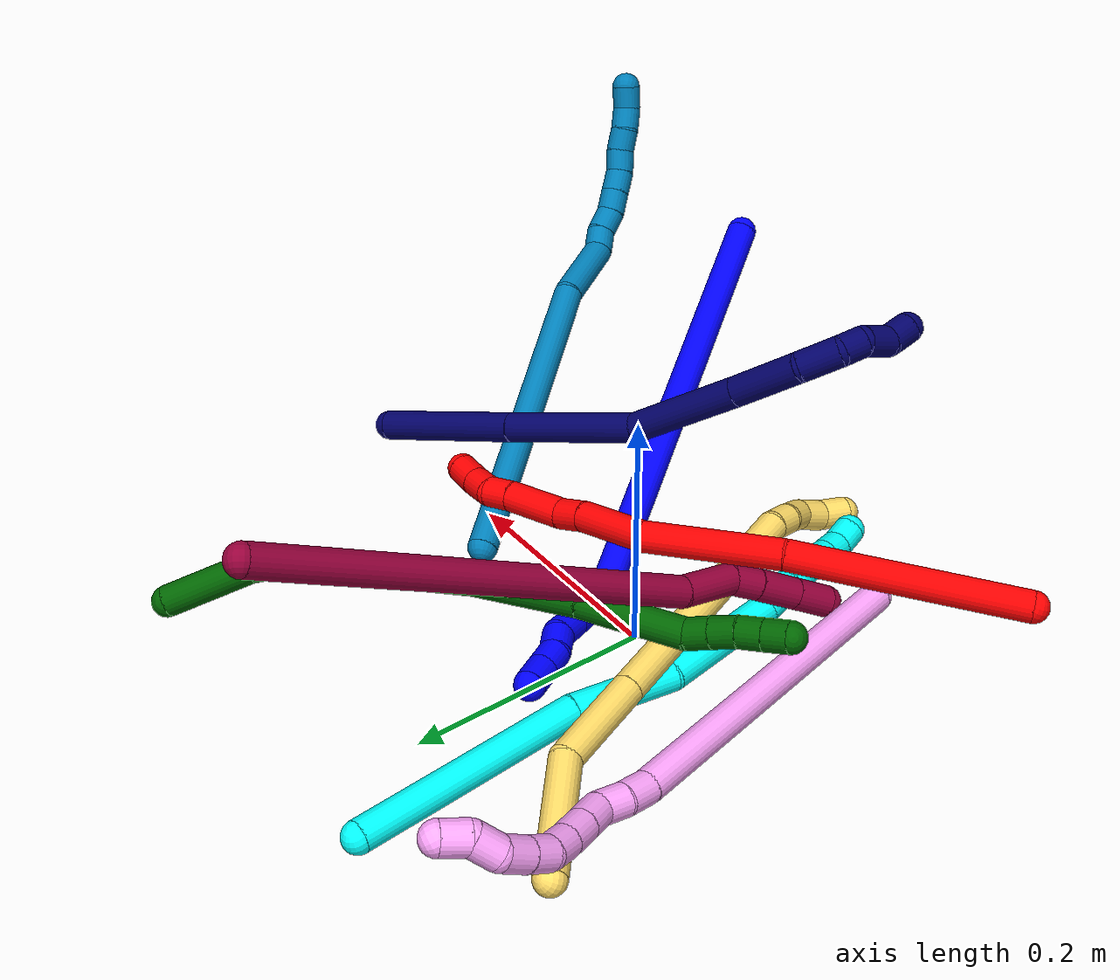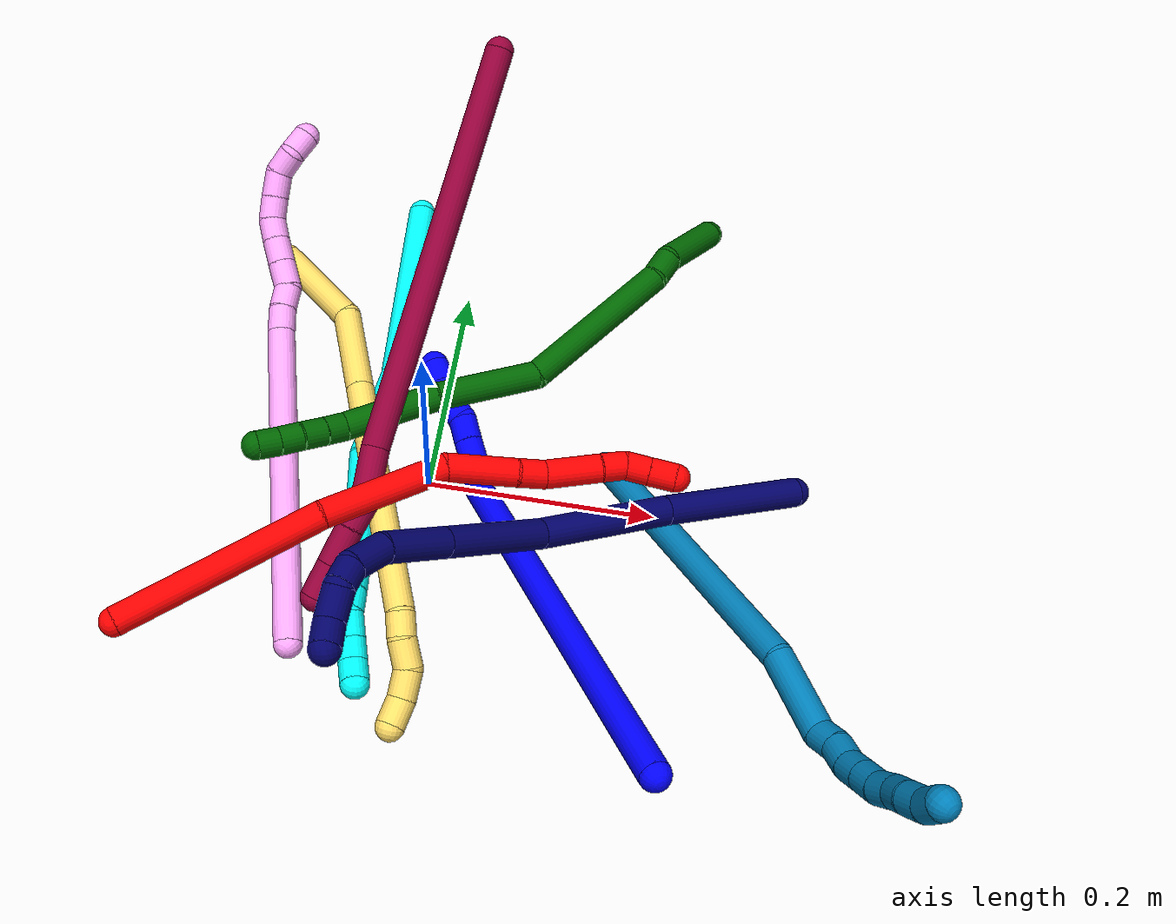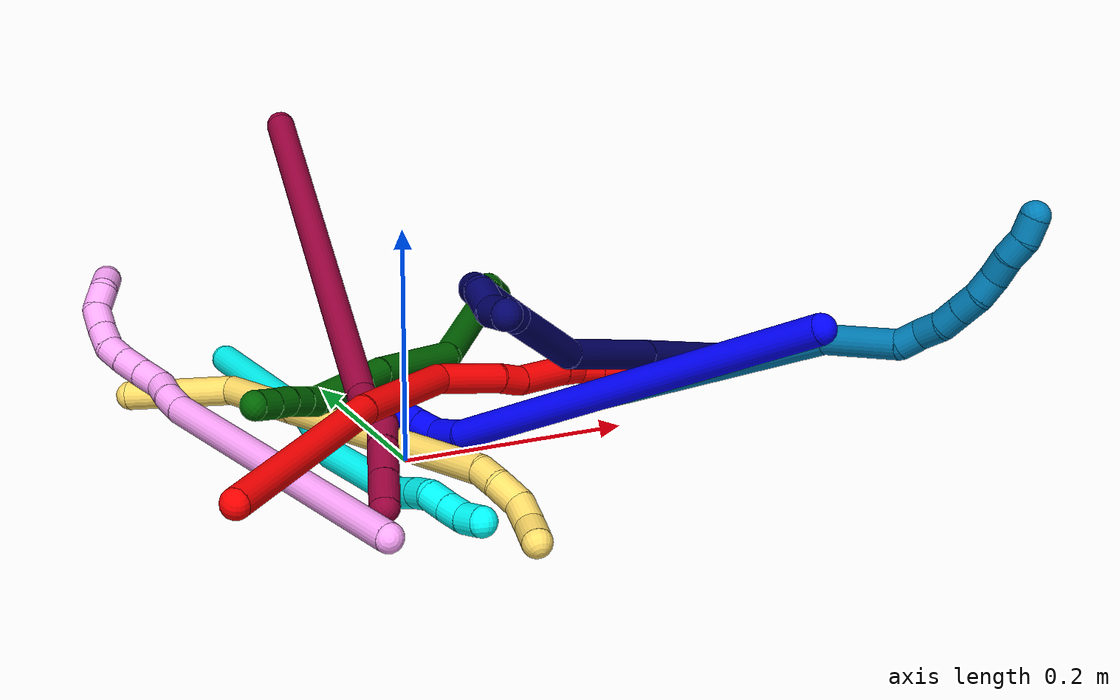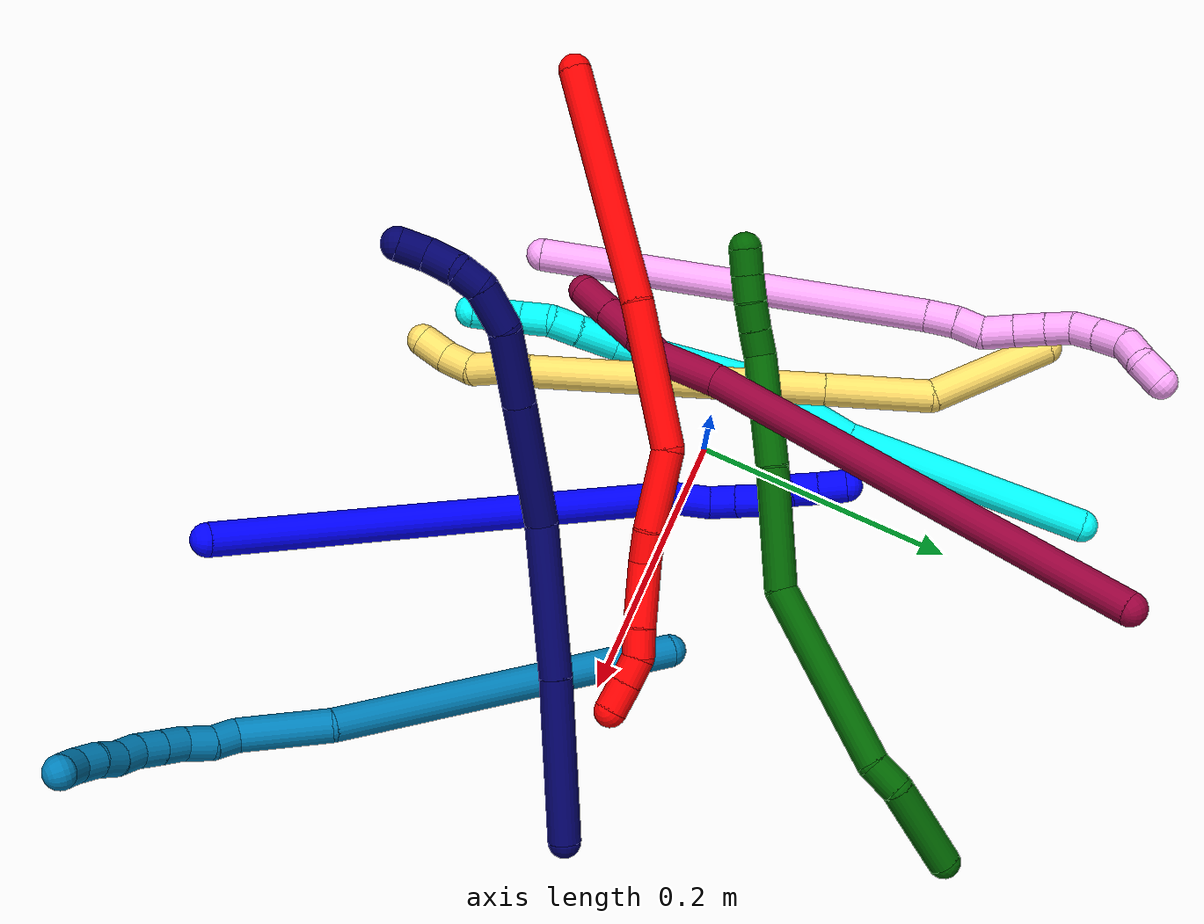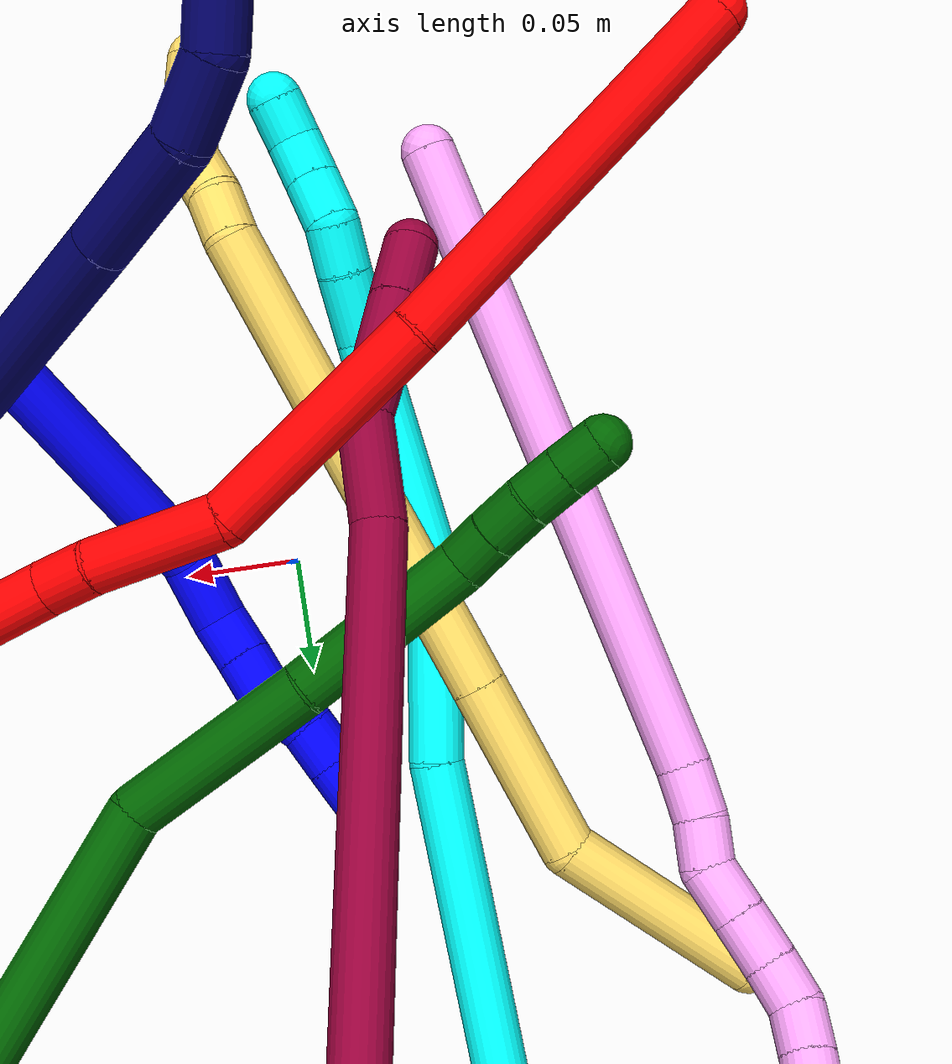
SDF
<sdf version="1.7">
 <world name="default">
  <plugin name="TubeGeneratorPlugin" filename="libtube_generator_plugin.so"/>
  <model name="photoneo_s_sensor">
   <static>1</static>
   <pose>0 0 2 1.57079 1.57079 3.14159</pose>
   <link name="link">
    <inertial><mass>0.1</mass></inertial>
    <sensor name="sensor" type="depth">
     <update_rate>30</update_rate>
     <camera>
      <horizontal_fov>1.22</horizontal_fov>
      <image><width>1920</width><height>1200</height><format>B8G8R8</format></image>
      <clip><near>0.1</near><far>4</far></clip>
      <depth_camera><output>points</output></depth_camera>
     </camera>
     <plugin name="camera_plugin" filename="libgazebo_ros_depth_camera.so">
      <baseline>0.2</baseline>
      <alwaysOn>1</alwaysOn>
      <updateRate>0.0</updateRate>
      <cameraName>camera_ir</cameraName>
      <imageTopicName>/camera/color/image_raw</imageTopicName>
      <cameraInfoTopicName>/camera/color/camera_info</cameraInfoTopicName>
      <depthImageTopicName>/camera/depth/image_raw</depthImageTopicName>
      <depthImageCameraInfoTopicName>/camera/depth/camera_info</depthImageCameraInfoTopicName>
      <pointCloudTopicName>/camera/depth/points</pointCloudTopicName>
      <frameName>fr_optical</frameName>
      <pointCloudCutoff>0.1</pointCloudCutoff>
      <pointCloudCutoffMax>2.0</pointCloudCutoffMax>
      <distortionK1>0</distortionK1>
      <distortionK2>0</distortionK2>
      <distortionK3>0</distortionK3>
      <distortionT1>0</distortionT1>
      <distortionT2>0</distortionT2>
      <CxPrime>0</CxPrime>
      <Cx>0</Cx>
      <Cy>0</Cy>
      <focalLength>0</focalLength>
      <hackBaseline>0</hackBaseline>
     </plugin>
    </sensor>
   </link>
  </model>
  <gravity>0 0 -9.8</gravity>
  <magnetic_field>6e-06 2.3e-05 -4.2e-05</magnetic_field>
  <atmosphere type="adiabatic"/>
  <physics name="default_physics" default="0" type="ode">
   <max_step_size>0.003</max_step_size>
   <real_time_factor>1</real_time_factor>
   <real_time_update_rate>1000</real_time_update_rate>
   <max_contacts>10000</max_contacts>
   <ode>
    <solver>
     <type>quick</type>
     <iters>100</iters>
     <sor>1.3</sor>
     <use_dynamic_moi_rescaling>0</use_dynamic_moi_rescaling>
    </solver>
    <constraints>
     <contact_max_correcting_vel>0</contact_max_correcting_vel>
     <contact_surface_layer>0.001</contact_surface_layer>
     <cfm>0</cfm>
     <erp>0.2</erp>
    </constraints>
   </ode>
  </physics>
  <scene><ambient>0.4 0.4 0.4 1</ambient><background>0.7 0.7 0.7 1</background><shadows>0</shadows></scene>
  <audio><device>default</device></audio>
  <spherical_coordinates>
   <surface_model>EARTH_WGS84</surface_model>
   <latitude_deg>0</latitude_deg>
   <longitude_deg>0</longitude_deg>
   <elevation>0</elevation>
   <heading_deg>0</heading_deg>
  </spherical_coordinates>
  <model name="bin">
   <static>1</static>
   <link name="bottom">
    <collision name="collision-bottom">
     <pose>0 0 -0.01 0 -0 0</pose>
     <geometry><box><size>0.8 0.6 0.02</size></box></geometry>
     <surface>
      <friction><ode><mu>100</mu><mu2>100</mu2></ode></friction>
      <contact><collide_bitmask>65535</collide_bitmask></contact>
     </surface>
    </collision>
   </link>
   <link name="west_wall">
    <collision name="collision-west_wall">
     <pose>-0.41 0 0.1 0 -0 0</pose>
     <geometry><box><size>0.02 0.6 0.2</size></box></geometry>
     <surface>
      <friction><ode><mu>100</mu><mu2>100</mu2></ode></friction>
      <contact><collide_bitmask>65535</collide_bitmask></contact>
     </surface>
    </collision>
   </link>
   <link name="east_wall">
    <collision name="collision-east_wall">
     <pose>0.41 0 0.1 0 -0 0</pose>
     <geometry><box><size>0.02 0.6 0.2</size></box></geometry>
     <surface>
      <friction><ode><mu>100</mu><mu2>100</mu2></ode></friction>
      <contact><collide_bitmask>65535</collide_bitmask></contact>
     </surface>
    </collision>
   </link>
   <link name="south_wall">
    <collision name="collision-south_wall">
     <pose>0 -0.31 0.1 0 -0 0</pose>
     <geometry><box><size>0.8 0.02 0.2</size></box></geometry>
     <surface>
      <friction><ode><mu>100</mu><mu2>100</mu2></ode></friction>
      <contact><collide_bitmask>65535</collide_bitmask></contact>
     </surface>
    </collision>
   </link>
   <link name="north_wall">
    <collision name="collision-north_wall">
     <pose>0 0.31 0.1 0 -0 0</pose>
     <geometry><box><size>0.8 0.02 0.2</size></box></geometry>
     <surface>
      <friction><ode><mu>100</mu><mu2>100</mu2></ode></friction>
      <contact><collide_bitmask>65535</collide_bitmask></contact>
     </surface>
    </collision>
   </link>
  </model>
  <model name="1">
   <static>0</static>
   <link name="1">
    <collision name="collision-cylinder-e_1_1_4">
     <pose>-0.010049 0.006523 -0.180957 -3.10556 -0.055438 1.98908</pose>
     <geometry><cylinder><radius>0.0125</radius><length>0.362706</length></cylinder></geometry>
     <surface>
      <friction><ode><mu>1.16</mu><mu2>1.16</mu2><slip1>0</slip1><slip2>0</slip2></ode></friction>
      <contact><ode><kp>1e+06</kp><kd>1</kd><max_vel>0</max_vel><min_depth>0.001</min_depth></ode></contact>
     </surface>
    </collision>
    <visual name="visual-cylinder-e_1_1_4">
     <pose>-0.010049 0.006523 -0.180957 -3.10556 -0.055438 1.98908</pose>
     <geometry><cylinder><radius>0.0125</radius><length>0.362706</length></cylinder></geometry>
     <material><ambient>0 0 1 1</ambient></material>
    </visual>
    <collision name="collision-cylinder-e_2_4_5">
     <pose>-0.019141 0.017984 -0.376568 -2.81655 0.06178 -0.372534</pose>
     <geometry><cylinder><radius>0.0125</radius><length>0.030987</length></cylinder></geometry>
     <surface>
      <friction><ode><mu>1.16</mu><mu2>1.16</mu2><slip1>0</slip1><slip2>0</slip2></ode></friction>
      <contact><ode><kp>1e+06</kp><kd>1</kd><max_vel>0</max_vel><min_depth>0.001</min_depth></ode></contact>
     </surface>
    </collision>
    <visual name="visual-cylinder-e_2_4_5">
     <pose>-0.019141 0.017984 -0.376568 -2.81655 0.06178 -0.372534</pose>
     <geometry><cylinder><radius>0.0125</radius><length>0.030987</length></cylinder></geometry>
     <material><ambient>0 0 1 1</ambient></material>
    </visual>
    <collision name="collision-cylinder-e_3_5_6">
     <pose>-0.020491 0.029134 -0.399525 -2.49933 -0.21892 0.638182</pose>
     <geometry><cylinder><radius>0.0125</radius><length>0.021246</length></cylinder></geometry>
     <surface>
      <friction><ode><mu>1.16</mu><mu2>1.16</mu2><slip1>0</slip1><slip2>0</slip2></ode></friction>
      <contact><ode><kp>1e+06</kp><kd>1</kd><max_vel>0</max_vel><min_depth>0.001</min_depth></ode></contact>
     </surface>
    </collision>
    <visual name="visual-cylinder-e_3_5_6">
     <pose>-0.020491 0.029134 -0.399525 -2.49933 -0.21892 0.638182</pose>
     <geometry><cylinder><radius>0.0125</radius><length>0.021246</length></cylinder></geometry>
     <material><ambient>0 0 1 1</ambient></material>
    </visual>
    <collision name="collision-cylinder-e_4_6_7">
     <pose>-0.025046 0.042118 -0.416288 -2.46649 -0.204519 0.56888</pose>
     <geometry><cylinder><radius>0.0125</radius><length>0.022135</length></cylinder></geometry>
     <surface>
      <friction><ode><mu>1.16</mu><mu2>1.16</mu2><slip1>0</slip1><slip2>0</slip2></ode></friction>
      <contact><ode><kp>1e+06</kp><kd>1</kd><max_vel>0</max_vel><min_depth>0.001</min_depth></ode></contact>
     </surface>
    </collision>
    <visual name="visual-cylinder-e_4_6_7">
     <pose>-0.025046 0.042118 -0.416288 -2.46649 -0.204519 0.56888</pose>
     <geometry><cylinder><radius>0.0125</radius><length>0.022135</length></cylinder></geometry>
     <material><ambient>0 0 1 1</ambient></material>
    </visual>
    <collision name="collision-cylinder-e_5_7_8">
     <pose>-0.031886 0.051495 -0.433471 -2.85143 -0.467189 2.04022</pose>
     <geometry><cylinder><radius>0.0125</radius><length>0.020394</length></cylinder></geometry>
     <surface>
      <friction><ode><mu>1.16</mu><mu2>1.16</mu2><slip1>0</slip1><slip2>0</slip2></ode></friction>
      <contact><ode><kp>1e+06</kp><kd>1</kd><max_vel>0</max_vel><min_depth>0.001</min_depth></ode></contact>
     </surface>
    </collision>
    <visual name="visual-cylinder-e_5_7_8">
     <pose>-0.031886 0.051495 -0.433471 -2.85143 -0.467189 2.04022</pose>
     <geometry><cylinder><radius>0.0125</radius><length>0.020394</length></cylinder></geometry>
     <material><ambient>0 0 1 1</ambient></material>
    </visual>
    <collision name="collision-cylinder-e_6_8_9">
     <pose>-0.038349 0.058723 -0.45122 -2.66821 -0.182431 0.724912</pose>
     <geometry><cylinder><radius>0.0125</radius><length>0.020623</length></cylinder></geometry>
     <surface>
      <friction><ode><mu>1.16</mu><mu2>1.16</mu2><slip1>0</slip1><slip2>0</slip2></ode></friction>
      <contact><ode><kp>1e+06</kp><kd>1</kd><max_vel>0</max_vel><min_depth>0.001</min_depth></ode></contact>
     </surface>
    </collision>
    <visual name="visual-cylinder-e_6_8_9">
     <pose>-0.038349 0.058723 -0.45122 -2.66821 -0.182431 0.724912</pose>
     <geometry><cylinder><radius>0.0125</radius><length>0.020623</length></cylinder></geometry>
     <material><ambient>0 0 1 1</ambient></material>
    </visual>
    <collision name="collision-cylinder-e_7_9_2">
     <pose>-0.042662 0.06852 -0.469588 -2.63585 -0.224773 0.823591</pose>
     <geometry><cylinder><radius>0.0125</radius><length>0.021909</length></cylinder></geometry>
     <surface>
      <friction><ode><mu>1.16</mu><mu2>1.16</mu2><slip1>0</slip1><slip2>0</slip2></ode></friction>
      <contact><ode><kp>1e+06</kp><kd>1</kd><max_vel>0</max_vel><min_depth>0.001</min_depth></ode></contact>
     </surface>
    </collision>
    <visual name="visual-cylinder-e_7_9_2">
     <pose>-0.042662 0.06852 -0.469588 -2.63585 -0.224773 0.823591</pose>
     <geometry><cylinder><radius>0.0125</radius><length>0.021909</length></cylinder></geometry>
     <material><ambient>0 0 1 1</ambient></material>
    </visual>
    <collision name="collision-sphere-2">
     <pose>-0.045103 0.073693 -0.47893 0 -0 0</pose>
     <geometry><sphere><radius>0.0125</radius></sphere></geometry>
     <surface>
      <friction><ode><mu>1.16</mu><mu2>1.16</mu2><slip1>0</slip1><slip2>0</slip2></ode></friction>
      <contact><ode><kp>1e+06</kp><kd>1</kd><max_vel>0</max_vel><min_depth>0.001</min_depth></ode></contact>
     </surface>
    </collision>
    <visual name="visual-sphere-2">
     <pose>-0.045103 0.073693 -0.47893 0 -0 0</pose>
     <geometry><sphere><radius>0.0125</radius></sphere></geometry>
     <material><ambient>0 0 1 1</ambient></material>
    </visual>
    <collision name="collision-sphere-9">
     <pose>-0.04022 0.063346 -0.460246 0 -0 0</pose>
     <geometry><sphere><radius>0.0125</radius></sphere></geometry>
     <surface>
      <friction><ode><mu>1.16</mu><mu2>1.16</mu2><slip1>0</slip1><slip2>0</slip2></ode></friction>
      <contact><ode><kp>1e+06</kp><kd>1</kd><max_vel>0</max_vel><min_depth>0.001</min_depth></ode></contact>
     </surface>
    </collision>
    <visual name="visual-sphere-9">
     <pose>-0.04022 0.063346 -0.460246 0 -0 0</pose>
     <geometry><sphere><radius>0.0125</radius></sphere></geometry>
     <material><ambient>0 0 1 1</ambient></material>
    </visual>
    <collision name="collision-sphere-4">
     <pose>-0.020097 0.013046 -0.361914 0 -0 0</pose>
     <geometry><sphere><radius>0.0125</radius></sphere></geometry>
     <surface>
      <friction><ode><mu>1.16</mu><mu2>1.16</mu2><slip1>0</slip1><slip2>0</slip2></ode></friction>
      <contact><ode><kp>1e+06</kp><kd>1</kd><max_vel>0</max_vel><min_depth>0.001</min_depth></ode></contact>
     </surface>
    </collision>
    <visual name="visual-sphere-4">
     <pose>-0.020097 0.013046 -0.361914 0 -0 0</pose>
     <geometry><sphere><radius>0.0125</radius></sphere></geometry>
     <material><ambient>0 0 1 1</ambient></material>
    </visual>
    <collision name="collision-sphere-1">
     <geometry><sphere><radius>0.0125</radius></sphere></geometry>
     <surface>
      <friction><ode><mu>1.16</mu><mu2>1.16</mu2><slip1>0</slip1><slip2>0</slip2></ode></friction>
      <contact><ode><kp>1e+06</kp><kd>1</kd><max_vel>0</max_vel><min_depth>0.001</min_depth></ode></contact>
     </surface>
    </collision>
    <visual name="visual-sphere-1">
     <geometry><sphere><radius>0.0125</radius></sphere></geometry>
     <material><ambient>0 0 1 1</ambient></material>
    </visual>
    <collision name="collision-sphere-8">
     <pose>-0.036479 0.0541 -0.442195 0 -0 0</pose>
     <geometry><sphere><radius>0.0125</radius></sphere></geometry>
     <surface>
      <friction><ode><mu>1.16</mu><mu2>1.16</mu2><slip1>0</slip1><slip2>0</slip2></ode></friction>
      <contact><ode><kp>1e+06</kp><kd>1</kd><max_vel>0</max_vel><min_depth>0.001</min_depth></ode></contact>
     </surface>
    </collision>
    <visual name="visual-sphere-8">
     <pose>-0.036479 0.0541 -0.442195 0 -0 0</pose>
     <geometry><sphere><radius>0.0125</radius></sphere></geometry>
     <material><ambient>0 0 1 1</ambient></material>
    </visual>
    <collision name="collision-sphere-5">
     <pose>-0.018184 0.022922 -0.391222 0 -0 0</pose>
     <geometry><sphere><radius>0.0125</radius></sphere></geometry>
     <surface>
      <friction><ode><mu>1.16</mu><mu2>1.16</mu2><slip1>0</slip1><slip2>0</slip2></ode></friction>
      <contact><ode><kp>1e+06</kp><kd>1</kd><max_vel>0</max_vel><min_depth>0.001</min_depth></ode></contact>
     </surface>
    </collision>
    <visual name="visual-sphere-5">
     <pose>-0.018184 0.022922 -0.391222 0 -0 0</pose>
     <geometry><sphere><radius>0.0125</radius></sphere></geometry>
     <material><ambient>0 0 1 1</ambient></material>
    </visual>
    <collision name="collision-sphere-6">
     <pose>-0.022798 0.035345 -0.407828 0 -0 0</pose>
     <geometry><sphere><radius>0.0125</radius></sphere></geometry>
     <surface>
      <friction><ode><mu>1.16</mu><mu2>1.16</mu2><slip1>0</slip1><slip2>0</slip2></ode></friction>
      <contact><ode><kp>1e+06</kp><kd>1</kd><max_vel>0</max_vel><min_depth>0.001</min_depth></ode></contact>
     </surface>
    </collision>
    <visual name="visual-sphere-6">
     <pose>-0.022798 0.035345 -0.407828 0 -0 0</pose>
     <geometry><sphere><radius>0.0125</radius></sphere></geometry>
     <material><ambient>0 0 1 1</ambient></material>
    </visual>
    <collision name="collision-sphere-7">
     <pose>-0.027294 0.04889 -0.424747 0 -0 0</pose>
     <geometry><sphere><radius>0.0125</radius></sphere></geometry>
     <surface>
      <friction><ode><mu>1.16</mu><mu2>1.16</mu2><slip1>0</slip1><slip2>0</slip2></ode></friction>
      <contact><ode><kp>1e+06</kp><kd>1</kd><max_vel>0</max_vel><min_depth>0.001</min_depth></ode></contact>
     </surface>
    </collision>
    <visual name="visual-sphere-7">
     <pose>-0.027294 0.04889 -0.424747 0 -0 0</pose>
     <geometry><sphere><radius>0.0125</radius></sphere></geometry>
     <material><ambient>0 0 1 1</ambient></material>
    </visual>
    <inertial>
     <pose>-0.015207 0.016474 -0.246879 0 -0 0</pose>
     <mass>0.5</mass>
     <inertia>
      <ixx>0.002031</ixx>
      <ixy>0</ixy>
      <ixz>0</ixz>
      <iyy>0.005272</iyy>
      <iyz>0</iyz>
      <izz>3.7e-05</izz>
     </inertia>
    </inertial>
   </link>
   <pose>0.220265 -0.288501 0.169025 1.03811 0.402343 0.28962</pose>
  </model>
  <model name="2">
   <static>0</static>
   <link name="2">
    <collision name="collision-cylinder-e_1_1_4">
     <pose>-0.032811 0.083884 -0.023309 -1.84184 -0.36041 0.470538</pose>
     <geometry><cylinder><radius>0.0125</radius><length>0.18608</length></cylinder></geometry>
     <surface>
      <friction><ode><mu>1.16</mu><mu2>1.16</mu2><slip1>0</slip1><slip2>0</slip2></ode></friction>
      <contact><ode><kp>1e+06</kp><kd>1</kd><max_vel>0</max_vel><min_depth>0.001</min_depth></ode></contact>
     </surface>
    </collision>
    <visual name="visual-cylinder-e_1_1_4">
     <pose>-0.032811 0.083884 -0.023309 -1.84184 -0.36041 0.470538</pose>
     <geometry><cylinder><radius>0.0125</radius><length>0.18608</length></cylinder></geometry>
     <material><ambient>1 0 0 1</ambient></material>
    </visual>
    <collision name="collision-cylinder-e_2_4_5">
     <pose>-0.07971 0.218052 -0.066578 -1.94865 -0.254731 0.372834</pose>
     <geometry><cylinder><radius>0.0125</radius><length>0.111809</length></cylinder></geometry>
     <surface>
      <friction><ode><mu>1.16</mu><mu2>1.16</mu2><slip1>0</slip1><slip2>0</slip2></ode></friction>
      <contact><ode><kp>1e+06</kp><kd>1</kd><max_vel>0</max_vel><min_depth>0.001</min_depth></ode></contact>
     </surface>
    </collision>
    <visual name="visual-cylinder-e_2_4_5">
     <pose>-0.07971 0.218052 -0.066578 -1.94865 -0.254731 0.372834</pose>
     <geometry><cylinder><radius>0.0125</radius><length>0.111809</length></cylinder></geometry>
     <material><ambient>1 0 0 1</ambient></material>
    </visual>
    <collision name="collision-cylinder-e_3_5_6">
     <pose>-0.088161 0.297226 -0.095486 -1.87118 0.184234 -0.249347</pose>
     <geometry><cylinder><radius>0.0125</radius><length>0.06153</length></cylinder></geometry>
     <surface>
      <friction><ode><mu>1.16</mu><mu2>1.16</mu2><slip1>0</slip1><slip2>0</slip2></ode></friction>
      <contact><ode><kp>1e+06</kp><kd>1</kd><max_vel>0</max_vel><min_depth>0.001</min_depth></ode></contact>
     </surface>
    </collision>
    <visual name="visual-cylinder-e_3_5_6">
     <pose>-0.088161 0.297226 -0.095486 -1.87118 0.184234 -0.249347</pose>
     <geometry><cylinder><radius>0.0125</radius><length>0.06153</length></cylinder></geometry>
     <material><ambient>1 0 0 1</ambient></material>
    </visual>
    <collision name="collision-cylinder-e_4_6_7">
     <pose>-0.080582 0.337008 -0.109727 -2.02313 0.159077 -0.253339</pose>
     <geometry><cylinder><radius>0.0125</radius><length>0.02453</length></cylinder></geometry>
     <surface>
      <friction><ode><mu>1.16</mu><mu2>1.16</mu2><slip1>0</slip1><slip2>0</slip2></ode></friction>
      <contact><ode><kp>1e+06</kp><kd>1</kd><max_vel>0</max_vel><min_depth>0.001</min_depth></ode></contact>
     </surface>
    </collision>
    <visual name="visual-cylinder-e_4_6_7">
     <pose>-0.080582 0.337008 -0.109727 -2.02313 0.159077 -0.253339</pose>
     <geometry><cylinder><radius>0.0125</radius><length>0.02453</length></cylinder></geometry>
     <material><ambient>1 0 0 1</ambient></material>
    </visual>
    <collision name="collision-cylinder-e_5_7_8">
     <pose>-0.078611 0.371725 -0.120901 -1.8128 0.001125 -0.001437</pose>
     <geometry><cylinder><radius>0.0125</radius><length>0.049078</length></cylinder></geometry>
     <surface>
      <friction><ode><mu>1.16</mu><mu2>1.16</mu2><slip1>0</slip1><slip2>0</slip2></ode></friction>
      <contact><ode><kp>1e+06</kp><kd>1</kd><max_vel>0</max_vel><min_depth>0.001</min_depth></ode></contact>
     </surface>
    </collision>
    <visual name="visual-cylinder-e_5_7_8">
     <pose>-0.078611 0.371725 -0.120901 -1.8128 0.001125 -0.001437</pose>
     <geometry><cylinder><radius>0.0125</radius><length>0.049078</length></cylinder></geometry>
     <material><ambient>1 0 0 1</ambient></material>
    </visual>
    <collision name="collision-cylinder-e_6_8_9">
     <pose>-0.078625 0.405884 -0.130453 -1.9121 -0.003727 0.005279</pose>
     <geometry><cylinder><radius>0.0125</radius><length>0.021937</length></cylinder></geometry>
     <surface>
      <friction><ode><mu>1.16</mu><mu2>1.16</mu2><slip1>0</slip1><slip2>0</slip2></ode></friction>
      <contact><ode><kp>1e+06</kp><kd>1</kd><max_vel>0</max_vel><min_depth>0.001</min_depth></ode></contact>
     </surface>
    </collision>
    <visual name="visual-cylinder-e_6_8_9">
     <pose>-0.078625 0.405884 -0.130453 -1.9121 -0.003727 0.005279</pose>
     <geometry><cylinder><radius>0.0125</radius><length>0.021937</length></cylinder></geometry>
     <material><ambient>1 0 0 1</ambient></material>
    </visual>
    <collision name="collision-cylinder-e_7_9_10">
     <pose>-0.07477 0.426042 -0.135549 -1.71487 0.374011 -0.430521</pose>
     <geometry><cylinder><radius>0.0125</radius><length>0.021324</length></cylinder></geometry>
     <surface>
      <friction><ode><mu>1.16</mu><mu2>1.16</mu2><slip1>0</slip1><slip2>0</slip2></ode></friction>
      <contact><ode><kp>1e+06</kp><kd>1</kd><max_vel>0</max_vel><min_depth>0.001</min_depth></ode></contact>
     </surface>
    </collision>
    <visual name="visual-cylinder-e_7_9_10">
     <pose>-0.07477 0.426042 -0.135549 -1.71487 0.374011 -0.430521</pose>
     <geometry><cylinder><radius>0.0125</radius><length>0.021324</length></cylinder></geometry>
     <material><ambient>1 0 0 1</ambient></material>
    </visual>
    <collision name="collision-cylinder-e_8_10_2">
     <pose>-0.066586 0.446906 -0.137488 -1.61726 0.370072 -0.38725</pose>
     <geometry><cylinder><radius>0.0125</radius><length>0.023712</length></cylinder></geometry>
     <surface>
      <friction><ode><mu>1.16</mu><mu2>1.16</mu2><slip1>0</slip1><slip2>0</slip2></ode></friction>
      <contact><ode><kp>1e+06</kp><kd>1</kd><max_vel>0</max_vel><min_depth>0.001</min_depth></ode></contact>
     </surface>
    </collision>
    <visual name="visual-cylinder-e_8_10_2">
     <pose>-0.066586 0.446906 -0.137488 -1.61726 0.370072 -0.38725</pose>
     <geometry><cylinder><radius>0.0125</radius><length>0.023712</length></cylinder></geometry>
     <material><ambient>1 0 0 1</ambient></material>
    </visual>
    <collision name="collision-sphere-2">
     <pose>-0.062298 0.457948 -0.138001 0 -0 0</pose>
     <geometry><sphere><radius>0.0125</radius></sphere></geometry>
     <surface>
      <friction><ode><mu>1.16</mu><mu2>1.16</mu2><slip1>0</slip1><slip2>0</slip2></ode></friction>
      <contact><ode><kp>1e+06</kp><kd>1</kd><max_vel>0</max_vel><min_depth>0.001</min_depth></ode></contact>
     </surface>
    </collision>
    <visual name="visual-sphere-2">
     <pose>-0.062298 0.457948 -0.138001 0 -0 0</pose>
     <geometry><sphere><radius>0.0125</radius></sphere></geometry>
     <material><ambient>1 0 0 1</ambient></material>
    </visual>
    <collision name="collision-sphere-10">
     <pose>-0.070875 0.435865 -0.136974 0 -0 0</pose>
     <geometry><sphere><radius>0.0125</radius></sphere></geometry>
     <surface>
      <friction><ode><mu>1.16</mu><mu2>1.16</mu2><slip1>0</slip1><slip2>0</slip2></ode></friction>
      <contact><ode><kp>1e+06</kp><kd>1</kd><max_vel>0</max_vel><min_depth>0.001</min_depth></ode></contact>
     </surface>
    </collision>
    <visual name="visual-sphere-10">
     <pose>-0.070875 0.435865 -0.136974 0 -0 0</pose>
     <geometry><sphere><radius>0.0125</radius></sphere></geometry>
     <material><ambient>1 0 0 1</ambient></material>
    </visual>
    <collision name="collision-sphere-9">
     <pose>-0.078665 0.41622 -0.134124 0 -0 0</pose>
     <geometry><sphere><radius>0.0125</radius></sphere></geometry>
     <surface>
      <friction><ode><mu>1.16</mu><mu2>1.16</mu2><slip1>0</slip1><slip2>0</slip2></ode></friction>
      <contact><ode><kp>1e+06</kp><kd>1</kd><max_vel>0</max_vel><min_depth>0.001</min_depth></ode></contact>
     </surface>
    </collision>
    <visual name="visual-sphere-9">
     <pose>-0.078665 0.41622 -0.134124 0 -0 0</pose>
     <geometry><sphere><radius>0.0125</radius></sphere></geometry>
     <material><ambient>1 0 0 1</ambient></material>
    </visual>
    <collision name="collision-sphere-4">
     <pose>-0.065622 0.167768 -0.046619 0 -0 0</pose>
     <geometry><sphere><radius>0.0125</radius></sphere></geometry>
     <surface>
      <friction><ode><mu>1.16</mu><mu2>1.16</mu2><slip1>0</slip1><slip2>0</slip2></ode></friction>
      <contact><ode><kp>1e+06</kp><kd>1</kd><max_vel>0</max_vel><min_depth>0.001</min_depth></ode></contact>
     </surface>
    </collision>
    <visual name="visual-sphere-4">
     <pose>-0.065622 0.167768 -0.046619 0 -0 0</pose>
     <geometry><sphere><radius>0.0125</radius></sphere></geometry>
     <material><ambient>1 0 0 1</ambient></material>
    </visual>
    <collision name="collision-sphere-1">
     <geometry><sphere><radius>0.0125</radius></sphere></geometry>
     <surface>
      <friction><ode><mu>1.16</mu><mu2>1.16</mu2><slip1>0</slip1><slip2>0</slip2></ode></friction>
      <contact><ode><kp>1e+06</kp><kd>1</kd><max_vel>0</max_vel><min_depth>0.001</min_depth></ode></contact>
     </surface>
    </collision>
    <visual name="visual-sphere-1">
     <geometry><sphere><radius>0.0125</radius></sphere></geometry>
     <material><ambient>1 0 0 1</ambient></material>
    </visual>
    <collision name="collision-sphere-8">
     <pose>-0.078584 0.395548 -0.126782 0 -0 0</pose>
     <geometry><sphere><radius>0.0125</radius></sphere></geometry>
     <surface>
      <friction><ode><mu>1.16</mu><mu2>1.16</mu2><slip1>0</slip1><slip2>0</slip2></ode></friction>
      <contact><ode><kp>1e+06</kp><kd>1</kd><max_vel>0</max_vel><min_depth>0.001</min_depth></ode></contact>
     </surface>
    </collision>
    <visual name="visual-sphere-8">
     <pose>-0.078584 0.395548 -0.126782 0 -0 0</pose>
     <geometry><sphere><radius>0.0125</radius></sphere></geometry>
     <material><ambient>1 0 0 1</ambient></material>
    </visual>
    <collision name="collision-sphere-5">
     <pose>-0.093797 0.268336 -0.086537 0 -0 0</pose>
     <geometry><sphere><radius>0.0125</radius></sphere></geometry>
     <surface>
      <friction><ode><mu>1.16</mu><mu2>1.16</mu2><slip1>0</slip1><slip2>0</slip2></ode></friction>
      <contact><ode><kp>1e+06</kp><kd>1</kd><max_vel>0</max_vel><min_depth>0.001</min_depth></ode></contact>
     </surface>
    </collision>
    <visual name="visual-sphere-5">
     <pose>-0.093797 0.268336 -0.086537 0 -0 0</pose>
     <geometry><sphere><radius>0.0125</radius></sphere></geometry>
     <material><ambient>1 0 0 1</ambient></material>
    </visual>
    <collision name="collision-sphere-6">
     <pose>-0.082525 0.326116 -0.104434 0 -0 0</pose>
     <geometry><sphere><radius>0.0125</radius></sphere></geometry>
     <surface>
      <friction><ode><mu>1.16</mu><mu2>1.16</mu2><slip1>0</slip1><slip2>0</slip2></ode></friction>
      <contact><ode><kp>1e+06</kp><kd>1</kd><max_vel>0</max_vel><min_depth>0.001</min_depth></ode></contact>
     </surface>
    </collision>
    <visual name="visual-sphere-6">
     <pose>-0.082525 0.326116 -0.104434 0 -0 0</pose>
     <geometry><sphere><radius>0.0125</radius></sphere></geometry>
     <material><ambient>1 0 0 1</ambient></material>
    </visual>
    <collision name="collision-sphere-7">
     <pose>-0.078639 0.347901 -0.11502 0 -0 0</pose>
     <geometry><sphere><radius>0.0125</radius></sphere></geometry>
     <surface>
      <friction><ode><mu>1.16</mu><mu2>1.16</mu2><slip1>0</slip1><slip2>0</slip2></ode></friction>
      <contact><ode><kp>1e+06</kp><kd>1</kd><max_vel>0</max_vel><min_depth>0.001</min_depth></ode></contact>
     </surface>
    </collision>
    <visual name="visual-sphere-7">
     <pose>-0.078639 0.347901 -0.11502 0 -0 0</pose>
     <geometry><sphere><radius>0.0125</radius></sphere></geometry>
     <material><ambient>1 0 0 1</ambient></material>
    </visual>
    <inertial>
     <pose>-0.06235 0.226748 -0.070588 0 -0 0</pose>
     <mass>0.5</mass>
     <inertia>
      <ixx>0.000864</ixx>
      <ixy>0</ixy>
      <ixz>0</ixz>
      <iyy>0.000215</iyy>
      <iyz>0</iyz>
      <izz>-0.000432</izz>
     </inertia>
    </inertial>
   </link>
   <pose>-0.215249 -0.203193 0.071728 0.176463 0.428768 -1.26296</pose>
  </model>
  <model name="3">
   <static>0</static>
   <link name="3">
    <collision name="collision-cylinder-e_1_1_4">
     <pose>0.005165 -0.090581 -0.026887 1.85934 0.054612 0.073163</pose>
     <geometry><cylinder><radius>0.0125</radius><length>0.189257</length></cylinder></geometry>
     <surface>
      <friction><ode><mu>1.16</mu><mu2>1.16</mu2><slip1>0</slip1><slip2>0</slip2></ode></friction>
      <contact><ode><kp>1e+06</kp><kd>1</kd><max_vel>0</max_vel><min_depth>0.001</min_depth></ode></contact>
     </surface>
    </collision>
    <visual name="visual-cylinder-e_1_1_4">
     <pose>0.005165 -0.090581 -0.026887 1.85934 0.054612 0.073163</pose>
     <geometry><cylinder><radius>0.0125</radius><length>0.189257</length></cylinder></geometry>
     <material><ambient>0.003922 1 0.996078 1</ambient></material>
    </visual>
    <collision name="collision-cylinder-e_2_4_5">
     <pose>0.004633 -0.221152 -0.06837 1.92077 -0.133042 -0.189897</pose>
     <geometry><cylinder><radius>0.0125</radius><length>0.085899</length></cylinder></geometry>
     <surface>
      <friction><ode><mu>1.16</mu><mu2>1.16</mu2><slip1>0</slip1><slip2>0</slip2></ode></friction>
      <contact><ode><kp>1e+06</kp><kd>1</kd><max_vel>0</max_vel><min_depth>0.001</min_depth></ode></contact>
     </surface>
    </collision>
    <visual name="visual-cylinder-e_2_4_5">
     <pose>0.004633 -0.221152 -0.06837 1.92077 -0.133042 -0.189897</pose>
     <geometry><cylinder><radius>0.0125</radius><length>0.085899</length></cylinder></geometry>
     <material><ambient>0.003922 1 0.996078 1</ambient></material>
    </visual>
    <collision name="collision-cylinder-e_3_5_6">
     <pose>0.006919 -0.312374 -0.098398 1.86336 0.148096 0.198982</pose>
     <geometry><cylinder><radius>0.0125</radius><length>0.108197</length></cylinder></geometry>
     <surface>
      <friction><ode><mu>1.16</mu><mu2>1.16</mu2><slip1>0</slip1><slip2>0</slip2></ode></friction>
      <contact><ode><kp>1e+06</kp><kd>1</kd><max_vel>0</max_vel><min_depth>0.001</min_depth></ode></contact>
     </surface>
    </collision>
    <visual name="visual-cylinder-e_3_5_6">
     <pose>0.006919 -0.312374 -0.098398 1.86336 0.148096 0.198982</pose>
     <geometry><cylinder><radius>0.0125</radius><length>0.108197</length></cylinder></geometry>
     <material><ambient>0.003922 1 0.996078 1</ambient></material>
    </visual>
    <collision name="collision-cylinder-e_4_6_7">
     <pose>0.016499 -0.379757 -0.113456 1.54765 0.098571 0.096319</pose>
     <geometry><cylinder><radius>0.0125</radius><length>0.032467</length></cylinder></geometry>
     <surface>
      <friction><ode><mu>1.16</mu><mu2>1.16</mu2><slip1>0</slip1><slip2>0</slip2></ode></friction>
      <contact><ode><kp>1e+06</kp><kd>1</kd><max_vel>0</max_vel><min_depth>0.001</min_depth></ode></contact>
     </surface>
    </collision>
    <visual name="visual-cylinder-e_4_6_7">
     <pose>0.016499 -0.379757 -0.113456 1.54765 0.098571 0.096319</pose>
     <geometry><cylinder><radius>0.0125</radius><length>0.032467</length></cylinder></geometry>
     <material><ambient>0.003922 1 0.996078 1</ambient></material>
    </visual>
    <collision name="collision-cylinder-e_5_7_8">
     <pose>0.01895 -0.407003 -0.113691 1.62563 0.076717 0.081039</pose>
     <geometry><cylinder><radius>0.0125</radius><length>0.02229</length></cylinder></geometry>
     <surface>
      <friction><ode><mu>1.16</mu><mu2>1.16</mu2><slip1>0</slip1><slip2>0</slip2></ode></friction>
      <contact><ode><kp>1e+06</kp><kd>1</kd><max_vel>0</max_vel><min_depth>0.001</min_depth></ode></contact>
     </surface>
    </collision>
    <visual name="visual-cylinder-e_5_7_8">
     <pose>0.01895 -0.407003 -0.113691 1.62563 0.076717 0.081039</pose>
     <geometry><cylinder><radius>0.0125</radius><length>0.02229</length></cylinder></geometry>
     <material><ambient>0.003922 1 0.996078 1</ambient></material>
    </visual>
    <collision name="collision-cylinder-e_6_8_9">
     <pose>0.022854 -0.427359 -0.119157 2.05379 0.283738 0.463858</pose>
     <geometry><cylinder><radius>0.0125</radius><length>0.021785</length></cylinder></geometry>
     <surface>
      <friction><ode><mu>1.16</mu><mu2>1.16</mu2><slip1>0</slip1><slip2>0</slip2></ode></friction>
      <contact><ode><kp>1e+06</kp><kd>1</kd><max_vel>0</max_vel><min_depth>0.001</min_depth></ode></contact>
     </surface>
    </collision>
    <visual name="visual-cylinder-e_6_8_9">
     <pose>0.022854 -0.427359 -0.119157 2.05379 0.283738 0.463858</pose>
     <geometry><cylinder><radius>0.0125</radius><length>0.021785</length></cylinder></geometry>
     <material><ambient>0.003922 1 0.996078 1</ambient></material>
    </visual>
    <collision name="collision-cylinder-e_7_9_10">
     <pose>0.028766 -0.44533 -0.128018 2.00175 0.290196 0.448362</pose>
     <geometry><cylinder><radius>0.0125</radius><length>0.020009</length></cylinder></geometry>
     <surface>
      <friction><ode><mu>1.16</mu><mu2>1.16</mu2><slip1>0</slip1><slip2>0</slip2></ode></friction>
      <contact><ode><kp>1e+06</kp><kd>1</kd><max_vel>0</max_vel><min_depth>0.001</min_depth></ode></contact>
     </surface>
    </collision>
    <visual name="visual-cylinder-e_7_9_10">
     <pose>0.028766 -0.44533 -0.128018 2.00175 0.290196 0.448362</pose>
     <geometry><cylinder><radius>0.0125</radius><length>0.020009</length></cylinder></geometry>
     <material><ambient>0.003922 1 0.996078 1</ambient></material>
    </visual>
    <collision name="collision-cylinder-e_8_10_2">
     <pose>0.034452 -0.463602 -0.133266 1.7001 0.284855 0.323649</pose>
     <geometry><cylinder><radius>0.0125</radius><length>0.020096</length></cylinder></geometry>
     <surface>
      <friction><ode><mu>1.16</mu><mu2>1.16</mu2><slip1>0</slip1><slip2>0</slip2></ode></friction>
      <contact><ode><kp>1e+06</kp><kd>1</kd><max_vel>0</max_vel><min_depth>0.001</min_depth></ode></contact>
     </surface>
    </collision>
    <visual name="visual-cylinder-e_8_10_2">
     <pose>0.034452 -0.463602 -0.133266 1.7001 0.284855 0.323649</pose>
     <geometry><cylinder><radius>0.0125</radius><length>0.020096</length></cylinder></geometry>
     <material><ambient>0.003922 1 0.996078 1</ambient></material>
    </visual>
    <collision name="collision-sphere-2">
     <pose>0.037276 -0.473165 -0.134509 0 -0 0</pose>
     <geometry><sphere><radius>0.0125</radius></sphere></geometry>
     <surface>
      <friction><ode><mu>1.16</mu><mu2>1.16</mu2><slip1>0</slip1><slip2>0</slip2></ode></friction>
      <contact><ode><kp>1e+06</kp><kd>1</kd><max_vel>0</max_vel><min_depth>0.001</min_depth></ode></contact>
     </surface>
    </collision>
    <visual name="visual-sphere-2">
     <pose>0.037276 -0.473165 -0.134509 0 -0 0</pose>
     <geometry><sphere><radius>0.0125</radius></sphere></geometry>
     <material><ambient>0.003922 1 0.996078 1</ambient></material>
    </visual>
    <collision name="collision-sphere-10">
     <pose>0.031628 -0.454039 -0.132022 0 -0 0</pose>
     <geometry><sphere><radius>0.0125</radius></sphere></geometry>
     <surface>
      <friction><ode><mu>1.16</mu><mu2>1.16</mu2><slip1>0</slip1><slip2>0</slip2></ode></friction>
      <contact><ode><kp>1e+06</kp><kd>1</kd><max_vel>0</max_vel><min_depth>0.001</min_depth></ode></contact>
     </surface>
    </collision>
    <visual name="visual-sphere-10">
     <pose>0.031628 -0.454039 -0.132022 0 -0 0</pose>
     <geometry><sphere><radius>0.0125</radius></sphere></geometry>
     <material><ambient>0.003922 1 0.996078 1</ambient></material>
    </visual>
    <collision name="collision-sphere-9">
     <pose>0.025903 -0.43662 -0.124013 0 -0 0</pose>
     <geometry><sphere><radius>0.0125</radius></sphere></geometry>
     <surface>
      <friction><ode><mu>1.16</mu><mu2>1.16</mu2><slip1>0</slip1><slip2>0</slip2></ode></friction>
      <contact><ode><kp>1e+06</kp><kd>1</kd><max_vel>0</max_vel><min_depth>0.001</min_depth></ode></contact>
     </surface>
    </collision>
    <visual name="visual-sphere-9">
     <pose>0.025903 -0.43662 -0.124013 0 -0 0</pose>
     <geometry><sphere><radius>0.0125</radius></sphere></geometry>
     <material><ambient>0.003922 1 0.996078 1</ambient></material>
    </visual>
    <collision name="collision-sphere-4">
     <pose>0.010331 -0.181163 -0.053774 0 -0 0</pose>
     <geometry><sphere><radius>0.0125</radius></sphere></geometry>
     <surface>
      <friction><ode><mu>1.16</mu><mu2>1.16</mu2><slip1>0</slip1><slip2>0</slip2></ode></friction>
      <contact><ode><kp>1e+06</kp><kd>1</kd><max_vel>0</max_vel><min_depth>0.001</min_depth></ode></contact>
     </surface>
    </collision>
    <visual name="visual-sphere-4">
     <pose>0.010331 -0.181163 -0.053774 0 -0 0</pose>
     <geometry><sphere><radius>0.0125</radius></sphere></geometry>
     <material><ambient>0.003922 1 0.996078 1</ambient></material>
    </visual>
    <collision name="collision-sphere-1">
     <geometry><sphere><radius>0.0125</radius></sphere></geometry>
     <surface>
      <friction><ode><mu>1.16</mu><mu2>1.16</mu2><slip1>0</slip1><slip2>0</slip2></ode></friction>
      <contact><ode><kp>1e+06</kp><kd>1</kd><max_vel>0</max_vel><min_depth>0.001</min_depth></ode></contact>
     </surface>
    </collision>
    <visual name="visual-sphere-1">
     <geometry><sphere><radius>0.0125</radius></sphere></geometry>
     <material><ambient>0.003922 1 0.996078 1</ambient></material>
    </visual>
    <collision name="collision-sphere-8">
     <pose>0.019805 -0.418099 -0.1143 0 -0 0</pose>
     <geometry><sphere><radius>0.0125</radius></sphere></geometry>
     <surface>
      <friction><ode><mu>1.16</mu><mu2>1.16</mu2><slip1>0</slip1><slip2>0</slip2></ode></friction>
      <contact><ode><kp>1e+06</kp><kd>1</kd><max_vel>0</max_vel><min_depth>0.001</min_depth></ode></contact>
     </surface>
    </collision>
    <visual name="visual-sphere-8">
     <pose>0.019805 -0.418099 -0.1143 0 -0 0</pose>
     <geometry><sphere><radius>0.0125</radius></sphere></geometry>
     <material><ambient>0.003922 1 0.996078 1</ambient></material>
    </visual>
    <collision name="collision-sphere-5">
     <pose>-0.001064 -0.261142 -0.082966 0 -0 0</pose>
     <geometry><sphere><radius>0.0125</radius></sphere></geometry>
     <surface>
      <friction><ode><mu>1.16</mu><mu2>1.16</mu2><slip1>0</slip1><slip2>0</slip2></ode></friction>
      <contact><ode><kp>1e+06</kp><kd>1</kd><max_vel>0</max_vel><min_depth>0.001</min_depth></ode></contact>
     </surface>
    </collision>
    <visual name="visual-sphere-5">
     <pose>-0.001064 -0.261142 -0.082966 0 -0 0</pose>
     <geometry><sphere><radius>0.0125</radius></sphere></geometry>
     <material><ambient>0.003922 1 0.996078 1</ambient></material>
    </visual>
    <collision name="collision-sphere-6">
     <pose>0.014901 -0.363607 -0.11383 0 -0 0</pose>
     <geometry><sphere><radius>0.0125</radius></sphere></geometry>
     <surface>
      <friction><ode><mu>1.16</mu><mu2>1.16</mu2><slip1>0</slip1><slip2>0</slip2></ode></friction>
      <contact><ode><kp>1e+06</kp><kd>1</kd><max_vel>0</max_vel><min_depth>0.001</min_depth></ode></contact>
     </surface>
    </collision>
    <visual name="visual-sphere-6">
     <pose>0.014901 -0.363607 -0.11383 0 -0 0</pose>
     <geometry><sphere><radius>0.0125</radius></sphere></geometry>
     <material><ambient>0.003922 1 0.996078 1</ambient></material>
    </visual>
    <collision name="collision-sphere-7">
     <pose>0.018096 -0.395907 -0.113082 0 -0 0</pose>
     <geometry><sphere><radius>0.0125</radius></sphere></geometry>
     <surface>
      <friction><ode><mu>1.16</mu><mu2>1.16</mu2><slip1>0</slip1><slip2>0</slip2></ode></friction>
      <contact><ode><kp>1e+06</kp><kd>1</kd><max_vel>0</max_vel><min_depth>0.001</min_depth></ode></contact>
     </surface>
    </collision>
    <visual name="visual-sphere-7">
     <pose>0.018096 -0.395907 -0.113082 0 -0 0</pose>
     <geometry><sphere><radius>0.0125</radius></sphere></geometry>
     <material><ambient>0.003922 1 0.996078 1</ambient></material>
    </visual>
    <inertial>
     <pose>0.009696 -0.237753 -0.071322 0 -0 0</pose>
     <mass>0.5</mass>
     <inertia>
      <ixx>0.000799</ixx>
      <ixy>0</ixy>
      <ixz>0</ixz>
      <iyy>-0.000189</iyy>
      <iyz>0</iyz>
      <izz>0.000662</izz>
     </inertia>
    </inertial>
   </link>
   <pose>-0.061464 0.286982 0.011497 -0.30737 0.052384 0.003288</pose>
  </model>
  <model name="4">
   <static>0</static>
   <link name="4">
    <collision name="collision-cylinder-e_1_1_4">
     <pose>-0.019997 0.094114 0.11372 -0.691343 -0.134651 0.048556</pose>
     <geometry><cylinder><radius>0.0125</radius><length>0.297923</length></cylinder></geometry>
     <surface>
      <friction><ode><mu>1.16</mu><mu2>1.16</mu2><slip1>0</slip1><slip2>0</slip2></ode></friction>
      <contact><ode><kp>1e+06</kp><kd>1</kd><max_vel>0</max_vel><min_depth>0.001</min_depth></ode></contact>
     </surface>
    </collision>
    <visual name="visual-cylinder-e_1_1_4">
     <pose>-0.019997 0.094114 0.11372 -0.691343 -0.134651 0.048556</pose>
     <geometry><cylinder><radius>0.0125</radius><length>0.297923</length></cylinder></geometry>
     <material><ambient>1 0.65098 0.996078 1</ambient></material>
    </visual>
    <collision name="collision-cylinder-e_2_4_5">
     <pose>-0.043439 0.195428 0.236211 -0.687353 -0.294726 0.106147</pose>
     <geometry><cylinder><radius>0.0125</radius><length>0.023718</length></cylinder></geometry>
     <surface>
      <friction><ode><mu>1.16</mu><mu2>1.16</mu2><slip1>0</slip1><slip2>0</slip2></ode></friction>
      <contact><ode><kp>1e+06</kp><kd>1</kd><max_vel>0</max_vel><min_depth>0.001</min_depth></ode></contact>
     </surface>
    </collision>
    <visual name="visual-cylinder-e_2_4_5">
     <pose>-0.043439 0.195428 0.236211 -0.687353 -0.294726 0.106147</pose>
     <geometry><cylinder><radius>0.0125</radius><length>0.023718</length></cylinder></geometry>
     <material><ambient>1 0.65098 0.996078 1</ambient></material>
    </visual>
    <collision name="collision-cylinder-e_3_5_6">
     <pose>-0.050636 0.207557 0.253913 -0.504228 -0.352479 0.091685</pose>
     <geometry><cylinder><radius>0.0125</radius><length>0.021738</length></cylinder></geometry>
     <surface>
      <friction><ode><mu>1.16</mu><mu2>1.16</mu2><slip1>0</slip1><slip2>0</slip2></ode></friction>
      <contact><ode><kp>1e+06</kp><kd>1</kd><max_vel>0</max_vel><min_depth>0.001</min_depth></ode></contact>
     </surface>
    </collision>
    <visual name="visual-cylinder-e_3_5_6">
     <pose>-0.050636 0.207557 0.253913 -0.504228 -0.352479 0.091685</pose>
     <geometry><cylinder><radius>0.0125</radius><length>0.021738</length></cylinder></geometry>
     <material><ambient>1 0.65098 0.996078 1</ambient></material>
    </visual>
    <collision name="collision-cylinder-e_4_6_7">
     <pose>-0.056728 0.222187 0.26965 -0.959033 -0.194909 0.101587</pose>
     <geometry><cylinder><radius>0.0125</radius><length>0.024161</length></cylinder></geometry>
     <surface>
      <friction><ode><mu>1.16</mu><mu2>1.16</mu2><slip1>0</slip1><slip2>0</slip2></ode></friction>
      <contact><ode><kp>1e+06</kp><kd>1</kd><max_vel>0</max_vel><min_depth>0.001</min_depth></ode></contact>
     </surface>
    </collision>
    <visual name="visual-cylinder-e_4_6_7">
     <pose>-0.056728 0.222187 0.26965 -0.959033 -0.194909 0.101587</pose>
     <geometry><cylinder><radius>0.0125</radius><length>0.024161</length></cylinder></geometry>
     <material><ambient>1 0.65098 0.996078 1</ambient></material>
    </visual>
    <collision name="collision-cylinder-e_5_7_8">
     <pose>-0.061636 0.241429 0.283132 -0.960291 -0.217068 0.113372</pose>
     <geometry><cylinder><radius>0.0125</radius><length>0.023846</length></cylinder></geometry>
     <surface>
      <friction><ode><mu>1.16</mu><mu2>1.16</mu2><slip1>0</slip1><slip2>0</slip2></ode></friction>
      <contact><ode><kp>1e+06</kp><kd>1</kd><max_vel>0</max_vel><min_depth>0.001</min_depth></ode></contact>
     </surface>
    </collision>
    <visual name="visual-cylinder-e_5_7_8">
     <pose>-0.061636 0.241429 0.283132 -0.960291 -0.217068 0.113372</pose>
     <geometry><cylinder><radius>0.0125</radius><length>0.023846</length></cylinder></geometry>
     <material><ambient>1 0.65098 0.996078 1</ambient></material>
    </visual>
    <collision name="collision-cylinder-e_6_8_9">
     <pose>-0.067229 0.259143 0.295502 -0.96224 -0.29486 0.154743</pose>
     <geometry><cylinder><radius>0.0125</radius><length>0.020823</length></cylinder></geometry>
     <surface>
      <friction><ode><mu>1.16</mu><mu2>1.16</mu2><slip1>0</slip1><slip2>0</slip2></ode></friction>
      <contact><ode><kp>1e+06</kp><kd>1</kd><max_vel>0</max_vel><min_depth>0.001</min_depth></ode></contact>
     </surface>
    </collision>
    <visual name="visual-cylinder-e_6_8_9">
     <pose>-0.067229 0.259143 0.295502 -0.96224 -0.29486 0.154743</pose>
     <geometry><cylinder><radius>0.0125</radius><length>0.020823</length></cylinder></geometry>
     <material><ambient>1 0.65098 0.996078 1</ambient></material>
    </visual>
    <collision name="collision-cylinder-e_7_9_10">
     <pose>-0.076494 0.273172 0.307393 -0.757134 -0.631839 0.258573</pose>
     <geometry><cylinder><radius>0.0125</radius><length>0.021128</length></cylinder></geometry>
     <surface>
      <friction><ode><mu>1.16</mu><mu2>1.16</mu2><slip1>0</slip1><slip2>0</slip2></ode></friction>
      <contact><ode><kp>1e+06</kp><kd>1</kd><max_vel>0</max_vel><min_depth>0.001</min_depth></ode></contact>
     </surface>
    </collision>
    <visual name="visual-cylinder-e_7_9_10">
     <pose>-0.076494 0.273172 0.307393 -0.757134 -0.631839 0.258573</pose>
     <geometry><cylinder><radius>0.0125</radius><length>0.021128</length></cylinder></geometry>
     <material><ambient>1 0.65098 0.996078 1</ambient></material>
    </visual>
    <collision name="collision-cylinder-e_8_10_11">
     <pose>-0.090529 0.285068 0.320139 -0.744953 -0.718732 0.291485</pose>
     <geometry><cylinder><radius>0.0125</radius><length>0.02368</length></cylinder></geometry>
     <surface>
      <friction><ode><mu>1.16</mu><mu2>1.16</mu2><slip1>0</slip1><slip2>0</slip2></ode></friction>
      <contact><ode><kp>1e+06</kp><kd>1</kd><max_vel>0</max_vel><min_depth>0.001</min_depth></ode></contact>
     </surface>
    </collision>
    <visual name="visual-cylinder-e_8_10_11">
     <pose>-0.090529 0.285068 0.320139 -0.744953 -0.718732 0.291485</pose>
     <geometry><cylinder><radius>0.0125</radius><length>0.02368</length></cylinder></geometry>
     <material><ambient>1 0.65098 0.996078 1</ambient></material>
    </visual>
    <collision name="collision-cylinder-e_9_11_12">
     <pose>-0.107885 0.291779 0.33203 -0.124848 -1.05808 0.073052</pose>
     <geometry><cylinder><radius>0.0125</radius><length>0.021942</length></cylinder></geometry>
     <surface>
      <friction><ode><mu>1.16</mu><mu2>1.16</mu2><slip1>0</slip1><slip2>0</slip2></ode></friction>
      <contact><ode><kp>1e+06</kp><kd>1</kd><max_vel>0</max_vel><min_depth>0.001</min_depth></ode></contact>
     </surface>
    </collision>
    <visual name="visual-cylinder-e_9_11_12">
     <pose>-0.107885 0.291779 0.33203 -0.124848 -1.05808 0.073052</pose>
     <geometry><cylinder><radius>0.0125</radius><length>0.021942</length></cylinder></geometry>
     <material><ambient>1 0.65098 0.996078 1</ambient></material>
    </visual>
    <collision name="collision-cylinder-e_10_12_2">
     <pose>-0.1229 0.293246 0.346331 -0.08862 -0.544979 0.024779</pose>
     <geometry><cylinder><radius>0.0125</radius><length>0.021041</length></cylinder></geometry>
     <surface>
      <friction><ode><mu>1.16</mu><mu2>1.16</mu2><slip1>0</slip1><slip2>0</slip2></ode></friction>
      <contact><ode><kp>1e+06</kp><kd>1</kd><max_vel>0</max_vel><min_depth>0.001</min_depth></ode></contact>
     </surface>
    </collision>
    <visual name="visual-cylinder-e_10_12_2">
     <pose>-0.1229 0.293246 0.346331 -0.08862 -0.544979 0.024779</pose>
     <geometry><cylinder><radius>0.0125</radius><length>0.021041</length></cylinder></geometry>
     <material><ambient>1 0.65098 0.996078 1</ambient></material>
    </visual>
    <collision name="collision-sphere-2">
     <pose>-0.128353 0.294042 0.355292 0 -0 0</pose>
     <geometry><sphere><radius>0.0125</radius></sphere></geometry>
     <surface>
      <friction><ode><mu>1.16</mu><mu2>1.16</mu2><slip1>0</slip1><slip2>0</slip2></ode></friction>
      <contact><ode><kp>1e+06</kp><kd>1</kd><max_vel>0</max_vel><min_depth>0.001</min_depth></ode></contact>
     </surface>
    </collision>
    <visual name="visual-sphere-2">
     <pose>-0.128353 0.294042 0.355292 0 -0 0</pose>
     <geometry><sphere><radius>0.0125</radius></sphere></geometry>
     <material><ambient>1 0.65098 0.996078 1</ambient></material>
    </visual>
    <collision name="collision-sphere-12">
     <pose>-0.117446 0.29245 0.33737 0 -0 0</pose>
     <geometry><sphere><radius>0.0125</radius></sphere></geometry>
     <surface>
      <friction><ode><mu>1.16</mu><mu2>1.16</mu2><slip1>0</slip1><slip2>0</slip2></ode></friction>
      <contact><ode><kp>1e+06</kp><kd>1</kd><max_vel>0</max_vel><min_depth>0.001</min_depth></ode></contact>
     </surface>
    </collision>
    <visual name="visual-sphere-12">
     <pose>-0.117446 0.29245 0.33737 0 -0 0</pose>
     <geometry><sphere><radius>0.0125</radius></sphere></geometry>
     <material><ambient>1 0.65098 0.996078 1</ambient></material>
    </visual>
    <collision name="collision-sphere-11">
     <pose>-0.098325 0.291109 0.32669 0 -0 0</pose>
     <geometry><sphere><radius>0.0125</radius></sphere></geometry>
     <surface>
      <friction><ode><mu>1.16</mu><mu2>1.16</mu2><slip1>0</slip1><slip2>0</slip2></ode></friction>
      <contact><ode><kp>1e+06</kp><kd>1</kd><max_vel>0</max_vel><min_depth>0.001</min_depth></ode></contact>
     </surface>
    </collision>
    <visual name="visual-sphere-11">
     <pose>-0.098325 0.291109 0.32669 0 -0 0</pose>
     <geometry><sphere><radius>0.0125</radius></sphere></geometry>
     <material><ambient>1 0.65098 0.996078 1</ambient></material>
    </visual>
    <collision name="collision-sphere-10">
     <pose>-0.082734 0.279027 0.313589 0 -0 0</pose>
     <geometry><sphere><radius>0.0125</radius></sphere></geometry>
     <surface>
      <friction><ode><mu>1.16</mu><mu2>1.16</mu2><slip1>0</slip1><slip2>0</slip2></ode></friction>
      <contact><ode><kp>1e+06</kp><kd>1</kd><max_vel>0</max_vel><min_depth>0.001</min_depth></ode></contact>
     </surface>
    </collision>
    <visual name="visual-sphere-10">
     <pose>-0.082734 0.279027 0.313589 0 -0 0</pose>
     <geometry><sphere><radius>0.0125</radius></sphere></geometry>
     <material><ambient>1 0.65098 0.996078 1</ambient></material>
    </visual>
    <collision name="collision-sphere-9">
     <pose>-0.070255 0.267317 0.301197 0 -0 0</pose>
     <geometry><sphere><radius>0.0125</radius></sphere></geometry>
     <surface>
      <friction><ode><mu>1.16</mu><mu2>1.16</mu2><slip1>0</slip1><slip2>0</slip2></ode></friction>
      <contact><ode><kp>1e+06</kp><kd>1</kd><max_vel>0</max_vel><min_depth>0.001</min_depth></ode></contact>
     </surface>
    </collision>
    <visual name="visual-sphere-9">
     <pose>-0.070255 0.267317 0.301197 0 -0 0</pose>
     <geometry><sphere><radius>0.0125</radius></sphere></geometry>
     <material><ambient>1 0.65098 0.996078 1</ambient></material>
    </visual>
    <collision name="collision-sphere-4">
     <pose>-0.039994 0.188228 0.22744 0 -0 0</pose>
     <geometry><sphere><radius>0.0125</radius></sphere></geometry>
     <surface>
      <friction><ode><mu>1.16</mu><mu2>1.16</mu2><slip1>0</slip1><slip2>0</slip2></ode></friction>
      <contact><ode><kp>1e+06</kp><kd>1</kd><max_vel>0</max_vel><min_depth>0.001</min_depth></ode></contact>
     </surface>
    </collision>
    <visual name="visual-sphere-4">
     <pose>-0.039994 0.188228 0.22744 0 -0 0</pose>
     <geometry><sphere><radius>0.0125</radius></sphere></geometry>
     <material><ambient>1 0.65098 0.996078 1</ambient></material>
    </visual>
    <collision name="collision-sphere-1">
     <geometry><sphere><radius>0.0125</radius></sphere></geometry>
     <surface>
      <friction><ode><mu>1.16</mu><mu2>1.16</mu2><slip1>0</slip1><slip2>0</slip2></ode></friction>
      <contact><ode><kp>1e+06</kp><kd>1</kd><max_vel>0</max_vel><min_depth>0.001</min_depth></ode></contact>
     </surface>
    </collision>
    <visual name="visual-sphere-1">
     <geometry><sphere><radius>0.0125</radius></sphere></geometry>
     <material><ambient>1 0.65098 0.996078 1</ambient></material>
    </visual>
    <collision name="collision-sphere-8">
     <pose>-0.064203 0.250969 0.289807 0 -0 0</pose>
     <geometry><sphere><radius>0.0125</radius></sphere></geometry>
     <surface>
      <friction><ode><mu>1.16</mu><mu2>1.16</mu2><slip1>0</slip1><slip2>0</slip2></ode></friction>
      <contact><ode><kp>1e+06</kp><kd>1</kd><max_vel>0</max_vel><min_depth>0.001</min_depth></ode></contact>
     </surface>
    </collision>
    <visual name="visual-sphere-8">
     <pose>-0.064203 0.250969 0.289807 0 -0 0</pose>
     <geometry><sphere><radius>0.0125</radius></sphere></geometry>
     <material><ambient>1 0.65098 0.996078 1</ambient></material>
    </visual>
    <collision name="collision-sphere-5">
     <pose>-0.046884 0.202628 0.244982 0 -0 0</pose>
     <geometry><sphere><radius>0.0125</radius></sphere></geometry>
     <surface>
      <friction><ode><mu>1.16</mu><mu2>1.16</mu2><slip1>0</slip1><slip2>0</slip2></ode></friction>
      <contact><ode><kp>1e+06</kp><kd>1</kd><max_vel>0</max_vel><min_depth>0.001</min_depth></ode></contact>
     </surface>
    </collision>
    <visual name="visual-sphere-5">
     <pose>-0.046884 0.202628 0.244982 0 -0 0</pose>
     <geometry><sphere><radius>0.0125</radius></sphere></geometry>
     <material><ambient>1 0.65098 0.996078 1</ambient></material>
    </visual>
    <collision name="collision-sphere-6">
     <pose>-0.054388 0.212485 0.262844 0 -0 0</pose>
     <geometry><sphere><radius>0.0125</radius></sphere></geometry>
     <surface>
      <friction><ode><mu>1.16</mu><mu2>1.16</mu2><slip1>0</slip1><slip2>0</slip2></ode></friction>
      <contact><ode><kp>1e+06</kp><kd>1</kd><max_vel>0</max_vel><min_depth>0.001</min_depth></ode></contact>
     </surface>
    </collision>
    <visual name="visual-sphere-6">
     <pose>-0.054388 0.212485 0.262844 0 -0 0</pose>
     <geometry><sphere><radius>0.0125</radius></sphere></geometry>
     <material><ambient>1 0.65098 0.996078 1</ambient></material>
    </visual>
    <collision name="collision-sphere-7">
     <pose>-0.059068 0.231889 0.276457 0 -0 0</pose>
     <geometry><sphere><radius>0.0125</radius></sphere></geometry>
     <surface>
      <friction><ode><mu>1.16</mu><mu2>1.16</mu2><slip1>0</slip1><slip2>0</slip2></ode></friction>
      <contact><ode><kp>1e+06</kp><kd>1</kd><max_vel>0</max_vel><min_depth>0.001</min_depth></ode></contact>
     </surface>
    </collision>
    <visual name="visual-sphere-7">
     <pose>-0.059068 0.231889 0.276457 0 -0 0</pose>
     <geometry><sphere><radius>0.0125</radius></sphere></geometry>
     <material><ambient>1 0.65098 0.996078 1</ambient></material>
    </visual>
    <inertial>
     <pose>-0.042084 0.157603 0.186139 0 -0 0</pose>
     <mass>0.5</mass>
     <inertia>
      <ixx>0.002305</ixx>
      <ixy>0</ixy>
      <ixz>0</ixz>
      <iyy>0.001858</iyy>
      <iyz>0</iyz>
      <izz>-0.001076</izz>
     </inertia>
    </inertial>
   </link>
   <pose>-0.086134 -0.174326 0.011464 2.3582 1.05438 -2.74609</pose>
  </model>
  <model name="5">
   <static>0</static>
   <link name="5">
    <collision name="collision-cylinder-e_1_1_4">
     <pose>0.01207 -0.043682 0.019634 1.14839 0.246895 0.16019</pose>
     <geometry><cylinder><radius>0.0125</radius><length>0.098778</length></cylinder></geometry>
     <surface>
      <friction><ode><mu>1.16</mu><mu2>1.16</mu2><slip1>0</slip1><slip2>0</slip2></ode></friction>
      <contact><ode><kp>1e+06</kp><kd>1</kd><max_vel>0</max_vel><min_depth>0.001</min_depth></ode></contact>
     </surface>
    </collision>
    <visual name="visual-cylinder-e_1_1_4">
     <pose>0.01207 -0.043682 0.019634 1.14839 0.246895 0.16019</pose>
     <geometry><cylinder><radius>0.0125</radius><length>0.098778</length></cylinder></geometry>
     <material><ambient>1 0.858824 0.4 1</ambient></material>
    </visual>
    <collision name="collision-cylinder-e_2_4_5">
     <pose>0.041386 -0.110382 0.068461 0.667664 0.434326 0.152745</pose>
     <geometry><cylinder><radius>0.0125</radius><length>0.081964</length></cylinder></geometry>
     <surface>
      <friction><ode><mu>1.16</mu><mu2>1.16</mu2><slip1>0</slip1><slip2>0</slip2></ode></friction>
      <contact><ode><kp>1e+06</kp><kd>1</kd><max_vel>0</max_vel><min_depth>0.001</min_depth></ode></contact>
     </surface>
    </collision>
    <visual name="visual-cylinder-e_2_4_5">
     <pose>0.041386 -0.110382 0.068461 0.667664 0.434326 0.152745</pose>
     <geometry><cylinder><radius>0.0125</radius><length>0.081964</length></cylinder></geometry>
     <material><ambient>1 0.858824 0.4 1</ambient></material>
    </visual>
    <collision name="collision-cylinder-e_3_5_6">
     <pose>0.105304 -0.196391 0.177369 0.668737 0.430633 0.151672</pose>
     <geometry><cylinder><radius>0.0125</radius><length>0.22361</length></cylinder></geometry>
     <surface>
      <friction><ode><mu>1.16</mu><mu2>1.16</mu2><slip1>0</slip1><slip2>0</slip2></ode></friction>
      <contact><ode><kp>1e+06</kp><kd>1</kd><max_vel>0</max_vel><min_depth>0.001</min_depth></ode></contact>
     </surface>
    </collision>
    <visual name="visual-cylinder-e_3_5_6">
     <pose>0.105304 -0.196391 0.177369 0.668737 0.430633 0.151672</pose>
     <geometry><cylinder><radius>0.0125</radius><length>0.22361</length></cylinder></geometry>
     <material><ambient>1 0.858824 0.4 1</ambient></material>
    </visual>
    <collision name="collision-cylinder-e_4_6_7">
     <pose>0.154668 -0.263645 0.266515 0.424608 0.254372 0.055114</pose>
     <geometry><cylinder><radius>0.0125</radius><length>0.021391</length></cylinder></geometry>
     <surface>
      <friction><ode><mu>1.16</mu><mu2>1.16</mu2><slip1>0</slip1><slip2>0</slip2></ode></friction>
      <contact><ode><kp>1e+06</kp><kd>1</kd><max_vel>0</max_vel><min_depth>0.001</min_depth></ode></contact>
     </surface>
    </collision>
    <visual name="visual-cylinder-e_4_6_7">
     <pose>0.154668 -0.263645 0.266515 0.424608 0.254372 0.055114</pose>
     <geometry><cylinder><radius>0.0125</radius><length>0.021391</length></cylinder></geometry>
     <material><ambient>1 0.858824 0.4 1</ambient></material>
    </visual>
    <collision name="collision-cylinder-e_5_7_8">
     <pose>0.157402 -0.273589 0.287267 0.464992 0.003341 0.000791</pose>
     <geometry><cylinder><radius>0.0125</radius><length>0.02533</length></cylinder></geometry>
     <surface>
      <friction><ode><mu>1.16</mu><mu2>1.16</mu2><slip1>0</slip1><slip2>0</slip2></ode></friction>
      <contact><ode><kp>1e+06</kp><kd>1</kd><max_vel>0</max_vel><min_depth>0.001</min_depth></ode></contact>
     </surface>
    </collision>
    <visual name="visual-cylinder-e_5_7_8">
     <pose>0.157402 -0.273589 0.287267 0.464992 0.003341 0.000791</pose>
     <geometry><cylinder><radius>0.0125</radius><length>0.02533</length></cylinder></geometry>
     <material><ambient>1 0.858824 0.4 1</ambient></material>
    </visual>
    <collision name="collision-cylinder-e_6_8_9">
     <pose>0.160051 -0.280106 0.310799 0.068546 0.209872 0.007222</pose>
     <geometry><cylinder><radius>0.0125</radius><length>0.02503</length></cylinder></geometry>
     <surface>
      <friction><ode><mu>1.16</mu><mu2>1.16</mu2><slip1>0</slip1><slip2>0</slip2></ode></friction>
      <contact><ode><kp>1e+06</kp><kd>1</kd><max_vel>0</max_vel><min_depth>0.001</min_depth></ode></contact>
     </surface>
    </collision>
    <visual name="visual-cylinder-e_6_8_9">
     <pose>0.160051 -0.280106 0.310799 0.068546 0.209872 0.007222</pose>
     <geometry><cylinder><radius>0.0125</radius><length>0.02503</length></cylinder></geometry>
     <material><ambient>1 0.858824 0.4 1</ambient></material>
    </visual>
    <collision name="collision-cylinder-e_7_9_2">
     <pose>0.168368 -0.280922 0.333507 -0.002145 0.498185 -0.000546</pose>
     <geometry><cylinder><radius>0.0125</radius><length>0.023896</length></cylinder></geometry>
     <surface>
      <friction><ode><mu>1.16</mu><mu2>1.16</mu2><slip1>0</slip1><slip2>0</slip2></ode></friction>
      <contact><ode><kp>1e+06</kp><kd>1</kd><max_vel>0</max_vel><min_depth>0.001</min_depth></ode></contact>
     </surface>
    </collision>
    <visual name="visual-cylinder-e_7_9_2">
     <pose>0.168368 -0.280922 0.333507 -0.002145 0.498185 -0.000546</pose>
     <geometry><cylinder><radius>0.0125</radius><length>0.023896</length></cylinder></geometry>
     <material><ambient>1 0.858824 0.4 1</ambient></material>
    </visual>
    <collision name="collision-sphere-2">
     <pose>0.174077 -0.280899 0.344003 0 -0 0</pose>
     <geometry><sphere><radius>0.0125</radius></sphere></geometry>
     <surface>
      <friction><ode><mu>1.16</mu><mu2>1.16</mu2><slip1>0</slip1><slip2>0</slip2></ode></friction>
      <contact><ode><kp>1e+06</kp><kd>1</kd><max_vel>0</max_vel><min_depth>0.001</min_depth></ode></contact>
     </surface>
    </collision>
    <visual name="visual-sphere-2">
     <pose>0.174077 -0.280899 0.344003 0 -0 0</pose>
     <geometry><sphere><radius>0.0125</radius></sphere></geometry>
     <material><ambient>1 0.858824 0.4 1</ambient></material>
    </visual>
    <collision name="collision-sphere-9">
     <pose>0.162658 -0.280944 0.323011 0 -0 0</pose>
     <geometry><sphere><radius>0.0125</radius></sphere></geometry>
     <surface>
      <friction><ode><mu>1.16</mu><mu2>1.16</mu2><slip1>0</slip1><slip2>0</slip2></ode></friction>
      <contact><ode><kp>1e+06</kp><kd>1</kd><max_vel>0</max_vel><min_depth>0.001</min_depth></ode></contact>
     </surface>
    </collision>
    <visual name="visual-sphere-9">
     <pose>0.162658 -0.280944 0.323011 0 -0 0</pose>
     <geometry><sphere><radius>0.0125</radius></sphere></geometry>
     <material><ambient>1 0.858824 0.4 1</ambient></material>
    </visual>
    <collision name="collision-sphere-4">
     <pose>0.024141 -0.087364 0.039267 0 -0 0</pose>
     <geometry><sphere><radius>0.0125</radius></sphere></geometry>
     <surface>
      <friction><ode><mu>1.16</mu><mu2>1.16</mu2><slip1>0</slip1><slip2>0</slip2></ode></friction>
      <contact><ode><kp>1e+06</kp><kd>1</kd><max_vel>0</max_vel><min_depth>0.001</min_depth></ode></contact>
     </surface>
    </collision>
    <visual name="visual-sphere-4">
     <pose>0.024141 -0.087364 0.039267 0 -0 0</pose>
     <geometry><sphere><radius>0.0125</radius></sphere></geometry>
     <material><ambient>1 0.858824 0.4 1</ambient></material>
    </visual>
    <collision name="collision-sphere-1">
     <geometry><sphere><radius>0.0125</radius></sphere></geometry>
     <surface>
      <friction><ode><mu>1.16</mu><mu2>1.16</mu2><slip1>0</slip1><slip2>0</slip2></ode></friction>
      <contact><ode><kp>1e+06</kp><kd>1</kd><max_vel>0</max_vel><min_depth>0.001</min_depth></ode></contact>
     </surface>
    </collision>
    <visual name="visual-sphere-1">
     <geometry><sphere><radius>0.0125</radius></sphere></geometry>
     <material><ambient>1 0.858824 0.4 1</ambient></material>
    </visual>
    <collision name="collision-sphere-8">
     <pose>0.157444 -0.279268 0.298588 0 -0 0</pose>
     <geometry><sphere><radius>0.0125</radius></sphere></geometry>
     <surface>
      <friction><ode><mu>1.16</mu><mu2>1.16</mu2><slip1>0</slip1><slip2>0</slip2></ode></friction>
      <contact><ode><kp>1e+06</kp><kd>1</kd><max_vel>0</max_vel><min_depth>0.001</min_depth></ode></contact>
     </surface>
    </collision>
    <visual name="visual-sphere-8">
     <pose>0.157444 -0.279268 0.298588 0 -0 0</pose>
     <geometry><sphere><radius>0.0125</radius></sphere></geometry>
     <material><ambient>1 0.858824 0.4 1</ambient></material>
    </visual>
    <collision name="collision-sphere-5">
     <pose>0.058631 -0.1334 0.097655 0 -0 0</pose>
     <geometry><sphere><radius>0.0125</radius></sphere></geometry>
     <surface>
      <friction><ode><mu>1.16</mu><mu2>1.16</mu2><slip1>0</slip1><slip2>0</slip2></ode></friction>
      <contact><ode><kp>1e+06</kp><kd>1</kd><max_vel>0</max_vel><min_depth>0.001</min_depth></ode></contact>
     </surface>
    </collision>
    <visual name="visual-sphere-5">
     <pose>0.058631 -0.1334 0.097655 0 -0 0</pose>
     <geometry><sphere><radius>0.0125</radius></sphere></geometry>
     <material><ambient>1 0.858824 0.4 1</ambient></material>
    </visual>
    <collision name="collision-sphere-6">
     <pose>0.151976 -0.259381 0.257083 0 -0 0</pose>
     <geometry><sphere><radius>0.0125</radius></sphere></geometry>
     <surface>
      <friction><ode><mu>1.16</mu><mu2>1.16</mu2><slip1>0</slip1><slip2>0</slip2></ode></friction>
      <contact><ode><kp>1e+06</kp><kd>1</kd><max_vel>0</max_vel><min_depth>0.001</min_depth></ode></contact>
     </surface>
    </collision>
    <visual name="visual-sphere-6">
     <pose>0.151976 -0.259381 0.257083 0 -0 0</pose>
     <geometry><sphere><radius>0.0125</radius></sphere></geometry>
     <material><ambient>1 0.858824 0.4 1</ambient></material>
    </visual>
    <collision name="collision-sphere-7">
     <pose>0.157359 -0.267909 0.275947 0 -0 0</pose>
     <geometry><sphere><radius>0.0125</radius></sphere></geometry>
     <surface>
      <friction><ode><mu>1.16</mu><mu2>1.16</mu2><slip1>0</slip1><slip2>0</slip2></ode></friction>
      <contact><ode><kp>1e+06</kp><kd>1</kd><max_vel>0</max_vel><min_depth>0.001</min_depth></ode></contact>
     </surface>
    </collision>
    <visual name="visual-sphere-7">
     <pose>0.157359 -0.267909 0.275947 0 -0 0</pose>
     <geometry><sphere><radius>0.0125</radius></sphere></geometry>
     <material><ambient>1 0.858824 0.4 1</ambient></material>
    </visual>
    <inertial>
     <pose>0.086913 -0.167142 0.151877 0 -0 0</pose>
     <mass>0.5</mass>
     <inertia>
      <ixx>0.00114</ixx>
      <ixy>0</ixy>
      <ixz>0</ixz>
      <iyy>0.000978</iyy>
      <iyz>0</iyz>
      <izz>0.000225</izz>
     </inertia>
    </inertial>
   </link>
   <pose>-0.175266 0.208028 0.017771 -2.78355 -0.887347 -2.10196</pose>
  </model>
  <model name="6">
   <static>0</static>
   <link name="6">
    <collision name="collision-cylinder-e_1_1_4">
     <pose>-0.020432 -0.028267 0.007934 1.29716 -0.608004 -0.466915</pose>
     <geometry><cylinder><radius>0.0125</radius><length>0.071538</length></cylinder></geometry>
     <surface>
      <friction><ode><mu>1.16</mu><mu2>1.16</mu2><slip1>0</slip1><slip2>0</slip2></ode></friction>
      <contact><ode><kp>1e+06</kp><kd>1</kd><max_vel>0</max_vel><min_depth>0.001</min_depth></ode></contact>
     </surface>
    </collision>
    <visual name="visual-cylinder-e_1_1_4">
     <pose>-0.020432 -0.028267 0.007934 1.29716 -0.608004 -0.466915</pose>
     <geometry><cylinder><radius>0.0125</radius><length>0.071538</length></cylinder></geometry>
     <material><ambient>0 0.392157 0.003922 1</ambient></material>
    </visual>
    <collision name="collision-cylinder-e_2_4_5">
     <pose>-0.049795 -0.065214 0.014161 1.76488 -0.79008 -0.938298</pose>
     <geometry><cylinder><radius>0.0125</radius><length>0.025142</length></cylinder></geometry>
     <surface>
      <friction><ode><mu>1.16</mu><mu2>1.16</mu2><slip1>0</slip1><slip2>0</slip2></ode></friction>
      <contact><ode><kp>1e+06</kp><kd>1</kd><max_vel>0</max_vel><min_depth>0.001</min_depth></ode></contact>
     </surface>
    </collision>
    <visual name="visual-cylinder-e_2_4_5">
     <pose>-0.049795 -0.065214 0.014161 1.76488 -0.79008 -0.938298</pose>
     <geometry><cylinder><radius>0.0125</radius><length>0.025142</length></cylinder></geometry>
     <material><ambient>0 0.392157 0.003922 1</ambient></material>
    </visual>
    <collision name="collision-cylinder-e_3_5_6">
     <pose>-0.12336 -0.107113 0.011981 1.58506 -1.09603 -1.10875</pose>
     <geometry><cylinder><radius>0.0125</radius><length>0.145345</length></cylinder></geometry>
     <surface>
      <friction><ode><mu>1.16</mu><mu2>1.16</mu2><slip1>0</slip1><slip2>0</slip2></ode></friction>
      <contact><ode><kp>1e+06</kp><kd>1</kd><max_vel>0</max_vel><min_depth>0.001</min_depth></ode></contact>
     </surface>
    </collision>
    <visual name="visual-cylinder-e_3_5_6">
     <pose>-0.12336 -0.107113 0.011981 1.58506 -1.09603 -1.10875</pose>
     <geometry><cylinder><radius>0.0125</radius><length>0.145345</length></cylinder></geometry>
     <material><ambient>0 0.392157 0.003922 1</ambient></material>
    </visual>
    <collision name="collision-cylinder-e_4_6_7">
     <pose>-0.226802 -0.154973 0.030798 0.649278 -1.01287 -0.369105</pose>
     <geometry><cylinder><radius>0.0125</radius><length>0.091488</length></cylinder></geometry>
     <surface>
      <friction><ode><mu>1.16</mu><mu2>1.16</mu2><slip1>0</slip1><slip2>0</slip2></ode></friction>
      <contact><ode><kp>1e+06</kp><kd>1</kd><max_vel>0</max_vel><min_depth>0.001</min_depth></ode></contact>
     </surface>
    </collision>
    <visual name="visual-cylinder-e_4_6_7">
     <pose>-0.226802 -0.154973 0.030798 0.649278 -1.01287 -0.369105</pose>
     <geometry><cylinder><radius>0.0125</radius><length>0.091488</length></cylinder></geometry>
     <material><ambient>0 0.392157 0.003922 1</ambient></material>
    </visual>
    <collision name="collision-cylinder-e_5_7_8">
     <pose>-0.304508 -0.180791 0.06354 0.693229 -1.1483 -0.459036</pose>
     <geometry><cylinder><radius>0.0125</radius><length>0.085299</length></cylinder></geometry>
     <surface>
      <friction><ode><mu>1.16</mu><mu2>1.16</mu2><slip1>0</slip1><slip2>0</slip2></ode></friction>
      <contact><ode><kp>1e+06</kp><kd>1</kd><max_vel>0</max_vel><min_depth>0.001</min_depth></ode></contact>
     </surface>
    </collision>
    <visual name="visual-cylinder-e_5_7_8">
     <pose>-0.304508 -0.180791 0.06354 0.693229 -1.1483 -0.459036</pose>
     <geometry><cylinder><radius>0.0125</radius><length>0.085299</length></cylinder></geometry>
     <material><ambient>0 0.392157 0.003922 1</ambient></material>
    </visual>
    <collision name="collision-cylinder-e_6_8_9">
     <pose>-0.350672 -0.197329 0.081375 0.88553 -0.809271 -0.400689</pose>
     <geometry><cylinder><radius>0.0125</radius><length>0.020073</length></cylinder></geometry>
     <surface>
      <friction><ode><mu>1.16</mu><mu2>1.16</mu2><slip1>0</slip1><slip2>0</slip2></ode></friction>
      <contact><ode><kp>1e+06</kp><kd>1</kd><max_vel>0</max_vel><min_depth>0.001</min_depth></ode></contact>
     </surface>
    </collision>
    <visual name="visual-cylinder-e_6_8_9">
     <pose>-0.350672 -0.197329 0.081375 0.88553 -0.809271 -0.400689</pose>
     <geometry><cylinder><radius>0.0125</radius><length>0.020073</length></cylinder></geometry>
     <material><ambient>0 0.392157 0.003922 1</ambient></material>
    </visual>
    <collision name="collision-cylinder-e_7_9_10">
     <pose>-0.365682 -0.207933 0.090566 0.828597 -0.827974 -0.381731</pose>
     <geometry><cylinder><radius>0.0125</radius><length>0.021034</length></cylinder></geometry>
     <surface>
      <friction><ode><mu>1.16</mu><mu2>1.16</mu2><slip1>0</slip1><slip2>0</slip2></ode></friction>
      <contact><ode><kp>1e+06</kp><kd>1</kd><max_vel>0</max_vel><min_depth>0.001</min_depth></ode></contact>
     </surface>
    </collision>
    <visual name="visual-cylinder-e_7_9_10">
     <pose>-0.365682 -0.207933 0.090566 0.828597 -0.827974 -0.381731</pose>
     <geometry><cylinder><radius>0.0125</radius><length>0.021034</length></cylinder></geometry>
     <material><ambient>0 0.392157 0.003922 1</ambient></material>
    </visual>
    <collision name="collision-cylinder-e_8_10_11">
     <pose>-0.381571 -0.217164 0.099647 0.750916 -0.948148 -0.399101</pose>
     <geometry><cylinder><radius>0.0125</radius><length>0.020046</length></cylinder></geometry>
     <surface>
      <friction><ode><mu>1.16</mu><mu2>1.16</mu2><slip1>0</slip1><slip2>0</slip2></ode></friction>
      <contact><ode><kp>1e+06</kp><kd>1</kd><max_vel>0</max_vel><min_depth>0.001</min_depth></ode></contact>
     </surface>
    </collision>
    <visual name="visual-cylinder-e_8_10_11">
     <pose>-0.381571 -0.217164 0.099647 0.750916 -0.948148 -0.399101</pose>
     <geometry><cylinder><radius>0.0125</radius><length>0.020046</length></cylinder></geometry>
     <material><ambient>0 0.392157 0.003922 1</ambient></material>
    </visual>
    <collision name="collision-cylinder-e_9_11_2">
     <pose>-0.397596 -0.225138 0.108645 0.70081 -0.905786 -0.352032</pose>
     <geometry><cylinder><radius>0.0125</radius><length>0.020035</length></cylinder></geometry>
     <surface>
      <friction><ode><mu>1.16</mu><mu2>1.16</mu2><slip1>0</slip1><slip2>0</slip2></ode></friction>
      <contact><ode><kp>1e+06</kp><kd>1</kd><max_vel>0</max_vel><min_depth>0.001</min_depth></ode></contact>
     </surface>
    </collision>
    <visual name="visual-cylinder-e_9_11_2">
     <pose>-0.397596 -0.225138 0.108645 0.70081 -0.905786 -0.352032</pose>
     <geometry><cylinder><radius>0.0125</radius><length>0.020035</length></cylinder></geometry>
     <material><ambient>0 0.392157 0.003922 1</ambient></material>
    </visual>
    <collision name="collision-sphere-2">
     <pose>-0.405479 -0.229124 0.11337 0 -0 0</pose>
     <geometry><sphere><radius>0.0125</radius></sphere></geometry>
     <surface>
      <friction><ode><mu>1.16</mu><mu2>1.16</mu2><slip1>0</slip1><slip2>0</slip2></ode></friction>
      <contact><ode><kp>1e+06</kp><kd>1</kd><max_vel>0</max_vel><min_depth>0.001</min_depth></ode></contact>
     </surface>
    </collision>
    <visual name="visual-sphere-2">
     <pose>-0.405479 -0.229124 0.11337 0 -0 0</pose>
     <geometry><sphere><radius>0.0125</radius></sphere></geometry>
     <material><ambient>0 0.392157 0.003922 1</ambient></material>
    </visual>
    <collision name="collision-sphere-11">
     <pose>-0.389713 -0.221152 0.10392 0 -0 0</pose>
     <geometry><sphere><radius>0.0125</radius></sphere></geometry>
     <surface>
      <friction><ode><mu>1.16</mu><mu2>1.16</mu2><slip1>0</slip1><slip2>0</slip2></ode></friction>
      <contact><ode><kp>1e+06</kp><kd>1</kd><max_vel>0</max_vel><min_depth>0.001</min_depth></ode></contact>
     </surface>
    </collision>
    <visual name="visual-sphere-11">
     <pose>-0.389713 -0.221152 0.10392 0 -0 0</pose>
     <geometry><sphere><radius>0.0125</radius></sphere></geometry>
     <material><ambient>0 0.392157 0.003922 1</ambient></material>
    </visual>
    <collision name="collision-sphere-10">
     <pose>-0.373429 -0.213175 0.095374 0 -0 0</pose>
     <geometry><sphere><radius>0.0125</radius></sphere></geometry>
     <surface>
      <friction><ode><mu>1.16</mu><mu2>1.16</mu2><slip1>0</slip1><slip2>0</slip2></ode></friction>
      <contact><ode><kp>1e+06</kp><kd>1</kd><max_vel>0</max_vel><min_depth>0.001</min_depth></ode></contact>
     </surface>
    </collision>
    <visual name="visual-sphere-10">
     <pose>-0.373429 -0.213175 0.095374 0 -0 0</pose>
     <geometry><sphere><radius>0.0125</radius></sphere></geometry>
     <material><ambient>0 0.392157 0.003922 1</ambient></material>
    </visual>
    <collision name="collision-sphere-9">
     <pose>-0.357936 -0.202691 0.085758 0 -0 0</pose>
     <geometry><sphere><radius>0.0125</radius></sphere></geometry>
     <surface>
      <friction><ode><mu>1.16</mu><mu2>1.16</mu2><slip1>0</slip1><slip2>0</slip2></ode></friction>
      <contact><ode><kp>1e+06</kp><kd>1</kd><max_vel>0</max_vel><min_depth>0.001</min_depth></ode></contact>
     </surface>
    </collision>
    <visual name="visual-sphere-9">
     <pose>-0.357936 -0.202691 0.085758 0 -0 0</pose>
     <geometry><sphere><radius>0.0125</radius></sphere></geometry>
     <material><ambient>0 0.392157 0.003922 1</ambient></material>
    </visual>
    <collision name="collision-sphere-4">
     <pose>-0.040865 -0.056533 0.015868 0 -0 0</pose>
     <geometry><sphere><radius>0.0125</radius></sphere></geometry>
     <surface>
      <friction><ode><mu>1.16</mu><mu2>1.16</mu2><slip1>0</slip1><slip2>0</slip2></ode></friction>
      <contact><ode><kp>1e+06</kp><kd>1</kd><max_vel>0</max_vel><min_depth>0.001</min_depth></ode></contact>
     </surface>
    </collision>
    <visual name="visual-sphere-4">
     <pose>-0.040865 -0.056533 0.015868 0 -0 0</pose>
     <geometry><sphere><radius>0.0125</radius></sphere></geometry>
     <material><ambient>0 0.392157 0.003922 1</ambient></material>
    </visual>
    <collision name="collision-sphere-1">
     <geometry><sphere><radius>0.0125</radius></sphere></geometry>
     <surface>
      <friction><ode><mu>1.16</mu><mu2>1.16</mu2><slip1>0</slip1><slip2>0</slip2></ode></friction>
      <contact><ode><kp>1e+06</kp><kd>1</kd><max_vel>0</max_vel><min_depth>0.001</min_depth></ode></contact>
     </surface>
    </collision>
    <visual name="visual-sphere-1">
     <geometry><sphere><radius>0.0125</radius></sphere></geometry>
     <material><ambient>0 0.392157 0.003922 1</ambient></material>
    </visual>
    <collision name="collision-sphere-8">
     <pose>-0.343408 -0.191967 0.076992 0 -0 0</pose>
     <geometry><sphere><radius>0.0125</radius></sphere></geometry>
     <surface>
      <friction><ode><mu>1.16</mu><mu2>1.16</mu2><slip1>0</slip1><slip2>0</slip2></ode></friction>
      <contact><ode><kp>1e+06</kp><kd>1</kd><max_vel>0</max_vel><min_depth>0.001</min_depth></ode></contact>
     </surface>
    </collision>
    <visual name="visual-sphere-8">
     <pose>-0.343408 -0.191967 0.076992 0 -0 0</pose>
     <geometry><sphere><radius>0.0125</radius></sphere></geometry>
     <material><ambient>0 0.392157 0.003922 1</ambient></material>
    </visual>
    <collision name="collision-sphere-5">
     <pose>-0.058726 -0.073895 0.012455 0 -0 0</pose>
     <geometry><sphere><radius>0.0125</radius></sphere></geometry>
     <surface>
      <friction><ode><mu>1.16</mu><mu2>1.16</mu2><slip1>0</slip1><slip2>0</slip2></ode></friction>
      <contact><ode><kp>1e+06</kp><kd>1</kd><max_vel>0</max_vel><min_depth>0.001</min_depth></ode></contact>
     </surface>
    </collision>
    <visual name="visual-sphere-5">
     <pose>-0.058726 -0.073895 0.012455 0 -0 0</pose>
     <geometry><sphere><radius>0.0125</radius></sphere></geometry>
     <material><ambient>0 0.392157 0.003922 1</ambient></material>
    </visual>
    <collision name="collision-sphere-6">
     <pose>-0.187995 -0.140331 0.011508 0 -0 0</pose>
     <geometry><sphere><radius>0.0125</radius></sphere></geometry>
     <surface>
      <friction><ode><mu>1.16</mu><mu2>1.16</mu2><slip1>0</slip1><slip2>0</slip2></ode></friction>
      <contact><ode><kp>1e+06</kp><kd>1</kd><max_vel>0</max_vel><min_depth>0.001</min_depth></ode></contact>
     </surface>
    </collision>
    <visual name="visual-sphere-6">
     <pose>-0.187995 -0.140331 0.011508 0 -0 0</pose>
     <geometry><sphere><radius>0.0125</radius></sphere></geometry>
     <material><ambient>0 0.392157 0.003922 1</ambient></material>
    </visual>
    <collision name="collision-sphere-7">
     <pose>-0.265609 -0.169616 0.050089 0 -0 0</pose>
     <geometry><sphere><radius>0.0125</radius></sphere></geometry>
     <surface>
      <friction><ode><mu>1.16</mu><mu2>1.16</mu2><slip1>0</slip1><slip2>0</slip2></ode></friction>
      <contact><ode><kp>1e+06</kp><kd>1</kd><max_vel>0</max_vel><min_depth>0.001</min_depth></ode></contact>
     </surface>
    </collision>
    <visual name="visual-sphere-7">
     <pose>-0.265609 -0.169616 0.050089 0 -0 0</pose>
     <geometry><sphere><radius>0.0125</radius></sphere></geometry>
     <material><ambient>0 0.392157 0.003922 1</ambient></material>
    </visual>
    <inertial>
     <pose>-0.195426 -0.132056 0.03723 0 -0 0</pose>
     <mass>0.5</mass>
     <inertia>
      <ixx>-4.1e-05</ixx>
      <ixy>0</ixy>
      <ixz>0</ixz>
      <iyy>0.000181</iyy>
      <iyz>0</iyz>
      <izz>0.00056</izz>
     </inertia>
    </inertial>
   </link>
   <pose>0.214643 0.288185 0.037434 -0.772942 -0.446519 0.552736</pose>
  </model>
  <model name="7">
   <static>0</static>
   <link name="7">
    <collision name="collision-cylinder-e_1_1_4">
     <pose>-0.010128 0.004068 -0.061779 -3.07585 -0.162156 2.37247</pose>
     <geometry><cylinder><radius>0.0125</radius><length>0.125471</length></cylinder></geometry>
     <surface>
      <friction><ode><mu>1.16</mu><mu2>1.16</mu2><slip1>0</slip1><slip2>0</slip2></ode></friction>
      <contact><ode><kp>1e+06</kp><kd>1</kd><max_vel>0</max_vel><min_depth>0.001</min_depth></ode></contact>
     </surface>
    </collision>
    <visual name="visual-cylinder-e_1_1_4">
     <pose>-0.010128 0.004068 -0.061779 -3.07585 -0.162156 2.37247</pose>
     <geometry><cylinder><radius>0.0125</radius><length>0.125471</length></cylinder></geometry>
     <material><ambient>0.003922 0 0.403922 1</ambient></material>
    </visual>
    <collision name="collision-cylinder-e_2_4_5">
     <pose>-0.030803 0.009887 -0.180503 -3.11084 -0.183037 2.80954</pose>
     <geometry><cylinder><radius>0.0125</radius><length>0.11588</length></cylinder></geometry>
     <surface>
      <friction><ode><mu>1.16</mu><mu2>1.16</mu2><slip1>0</slip1><slip2>0</slip2></ode></friction>
      <contact><ode><kp>1e+06</kp><kd>1</kd><max_vel>0</max_vel><min_depth>0.001</min_depth></ode></contact>
     </surface>
    </collision>
    <visual name="visual-cylinder-e_2_4_5">
     <pose>-0.030803 0.009887 -0.180503 -3.11084 -0.183037 2.80954</pose>
     <geometry><cylinder><radius>0.0125</radius><length>0.11588</length></cylinder></geometry>
     <material><ambient>0.003922 0 0.403922 1</ambient></material>
    </visual>
    <collision name="collision-cylinder-e_3_5_6">
     <pose>-0.062414 0.020755 -0.280589 -2.93335 -0.445678 2.27739</pose>
     <geometry><cylinder><radius>0.0125</radius><length>0.097734</length></cylinder></geometry>
     <surface>
      <friction><ode><mu>1.16</mu><mu2>1.16</mu2><slip1>0</slip1><slip2>0</slip2></ode></friction>
      <contact><ode><kp>1e+06</kp><kd>1</kd><max_vel>0</max_vel><min_depth>0.001</min_depth></ode></contact>
     </surface>
    </collision>
    <visual name="visual-cylinder-e_3_5_6">
     <pose>-0.062414 0.020755 -0.280589 -2.93335 -0.445678 2.27739</pose>
     <geometry><cylinder><radius>0.0125</radius><length>0.097734</length></cylinder></geometry>
     <material><ambient>0.003922 0 0.403922 1</ambient></material>
    </visual>
    <collision name="collision-cylinder-e_4_6_7">
     <pose>-0.096511 0.035507 -0.349216 -2.92396 -0.463062 2.27373</pose>
     <geometry><cylinder><radius>0.0125</radius><length>0.058346</length></cylinder></geometry>
     <surface>
      <friction><ode><mu>1.16</mu><mu2>1.16</mu2><slip1>0</slip1><slip2>0</slip2></ode></friction>
      <contact><ode><kp>1e+06</kp><kd>1</kd><max_vel>0</max_vel><min_depth>0.001</min_depth></ode></contact>
     </surface>
    </collision>
    <visual name="visual-cylinder-e_4_6_7">
     <pose>-0.096511 0.035507 -0.349216 -2.92396 -0.463062 2.27373</pose>
     <geometry><cylinder><radius>0.0125</radius><length>0.058346</length></cylinder></geometry>
     <material><ambient>0.003922 0 0.403922 1</ambient></material>
    </visual>
    <collision name="collision-cylinder-e_5_7_8">
     <pose>-0.11912 0.039132 -0.38852 2.99709 -0.601197 -2.68284</pose>
     <geometry><cylinder><radius>0.0125</radius><length>0.033869</length></cylinder></geometry>
     <surface>
      <friction><ode><mu>1.16</mu><mu2>1.16</mu2><slip1>0</slip1><slip2>0</slip2></ode></friction>
      <contact><ode><kp>1e+06</kp><kd>1</kd><max_vel>0</max_vel><min_depth>0.001</min_depth></ode></contact>
     </surface>
    </collision>
    <visual name="visual-cylinder-e_5_7_8">
     <pose>-0.11912 0.039132 -0.38852 2.99709 -0.601197 -2.68284</pose>
     <geometry><cylinder><radius>0.0125</radius><length>0.033869</length></cylinder></geometry>
     <material><ambient>0.003922 0 0.403922 1</ambient></material>
    </visual>
    <collision name="collision-cylinder-e_6_8_9">
     <pose>-0.135122 0.032141 -0.408242 2.44075 -0.693845 -1.55991</pose>
     <geometry><cylinder><radius>0.0125</radius><length>0.020088</length></cylinder></geometry>
     <surface>
      <friction><ode><mu>1.16</mu><mu2>1.16</mu2><slip1>0</slip1><slip2>0</slip2></ode></friction>
      <contact><ode><kp>1e+06</kp><kd>1</kd><max_vel>0</max_vel><min_depth>0.001</min_depth></ode></contact>
     </surface>
    </collision>
    <visual name="visual-cylinder-e_6_8_9">
     <pose>-0.135122 0.032141 -0.408242 2.44075 -0.693845 -1.55991</pose>
     <geometry><cylinder><radius>0.0125</radius><length>0.020088</length></cylinder></geometry>
     <material><ambient>0.003922 0 0.403922 1</ambient></material>
    </visual>
    <collision name="collision-cylinder-e_7_9_10">
     <pose>-0.145756 0.016051 -0.419561 2.02448 -0.328277 -0.51815</pose>
     <geometry><cylinder><radius>0.0125</radius><length>0.026116</length></cylinder></geometry>
     <surface>
      <friction><ode><mu>1.16</mu><mu2>1.16</mu2><slip1>0</slip1><slip2>0</slip2></ode></friction>
      <contact><ode><kp>1e+06</kp><kd>1</kd><max_vel>0</max_vel><min_depth>0.001</min_depth></ode></contact>
     </surface>
    </collision>
    <visual name="visual-cylinder-e_7_9_10">
     <pose>-0.145756 0.016051 -0.419561 2.02448 -0.328277 -0.51815</pose>
     <geometry><cylinder><radius>0.0125</radius><length>0.026116</length></cylinder></geometry>
     <material><ambient>0.003922 0 0.403922 1</ambient></material>
    </visual>
    <collision name="collision-cylinder-e_8_10_2">
     <pose>-0.15815 -0.001877 -0.428588 2.05775 -0.814959 -1.24403</pose>
     <geometry><cylinder><radius>0.0125</radius><length>0.022495</length></cylinder></geometry>
     <surface>
      <friction><ode><mu>1.16</mu><mu2>1.16</mu2><slip1>0</slip1><slip2>0</slip2></ode></friction>
      <contact><ode><kp>1e+06</kp><kd>1</kd><max_vel>0</max_vel><min_depth>0.001</min_depth></ode></contact>
     </surface>
    </collision>
    <visual name="visual-cylinder-e_8_10_2">
     <pose>-0.15815 -0.001877 -0.428588 2.05775 -0.814959 -1.24403</pose>
     <geometry><cylinder><radius>0.0125</radius><length>0.022495</length></cylinder></geometry>
     <material><ambient>0.003922 0 0.403922 1</ambient></material>
    </visual>
    <collision name="collision-sphere-2">
     <pose>-0.166335 -0.008695 -0.432198 0 -0 0</pose>
     <geometry><sphere><radius>0.0125</radius></sphere></geometry>
     <surface>
      <friction><ode><mu>1.16</mu><mu2>1.16</mu2><slip1>0</slip1><slip2>0</slip2></ode></friction>
      <contact><ode><kp>1e+06</kp><kd>1</kd><max_vel>0</max_vel><min_depth>0.001</min_depth></ode></contact>
     </surface>
    </collision>
    <visual name="visual-sphere-2">
     <pose>-0.166335 -0.008695 -0.432198 0 -0 0</pose>
     <geometry><sphere><radius>0.0125</radius></sphere></geometry>
     <material><ambient>0.003922 0 0.403922 1</ambient></material>
    </visual>
    <collision name="collision-sphere-10">
     <pose>-0.149966 0.004941 -0.424978 0 -0 0</pose>
     <geometry><sphere><radius>0.0125</radius></sphere></geometry>
     <surface>
      <friction><ode><mu>1.16</mu><mu2>1.16</mu2><slip1>0</slip1><slip2>0</slip2></ode></friction>
      <contact><ode><kp>1e+06</kp><kd>1</kd><max_vel>0</max_vel><min_depth>0.001</min_depth></ode></contact>
     </surface>
    </collision>
    <visual name="visual-sphere-10">
     <pose>-0.149966 0.004941 -0.424978 0 -0 0</pose>
     <geometry><sphere><radius>0.0125</radius></sphere></geometry>
     <material><ambient>0.003922 0 0.403922 1</ambient></material>
    </visual>
    <collision name="collision-sphere-9">
     <pose>-0.141546 0.027162 -0.414144 0 -0 0</pose>
     <geometry><sphere><radius>0.0125</radius></sphere></geometry>
     <surface>
      <friction><ode><mu>1.16</mu><mu2>1.16</mu2><slip1>0</slip1><slip2>0</slip2></ode></friction>
      <contact><ode><kp>1e+06</kp><kd>1</kd><max_vel>0</max_vel><min_depth>0.001</min_depth></ode></contact>
     </surface>
    </collision>
    <visual name="visual-sphere-9">
     <pose>-0.141546 0.027162 -0.414144 0 -0 0</pose>
     <geometry><sphere><radius>0.0125</radius></sphere></geometry>
     <material><ambient>0.003922 0 0.403922 1</ambient></material>
    </visual>
    <collision name="collision-sphere-4">
     <pose>-0.020257 0.008135 -0.123558 0 -0 0</pose>
     <geometry><sphere><radius>0.0125</radius></sphere></geometry>
     <surface>
      <friction><ode><mu>1.16</mu><mu2>1.16</mu2><slip1>0</slip1><slip2>0</slip2></ode></friction>
      <contact><ode><kp>1e+06</kp><kd>1</kd><max_vel>0</max_vel><min_depth>0.001</min_depth></ode></contact>
     </surface>
    </collision>
    <visual name="visual-sphere-4">
     <pose>-0.020257 0.008135 -0.123558 0 -0 0</pose>
     <geometry><sphere><radius>0.0125</radius></sphere></geometry>
     <material><ambient>0.003922 0 0.403922 1</ambient></material>
    </visual>
    <collision name="collision-sphere-1">
     <geometry><sphere><radius>0.0125</radius></sphere></geometry>
     <surface>
      <friction><ode><mu>1.16</mu><mu2>1.16</mu2><slip1>0</slip1><slip2>0</slip2></ode></friction>
      <contact><ode><kp>1e+06</kp><kd>1</kd><max_vel>0</max_vel><min_depth>0.001</min_depth></ode></contact>
     </surface>
    </collision>
    <visual name="visual-sphere-1">
     <geometry><sphere><radius>0.0125</radius></sphere></geometry>
     <material><ambient>0.003922 0 0.403922 1</ambient></material>
    </visual>
    <collision name="collision-sphere-8">
     <pose>-0.128699 0.037121 -0.40234 0 -0 0</pose>
     <geometry><sphere><radius>0.0125</radius></sphere></geometry>
     <surface>
      <friction><ode><mu>1.16</mu><mu2>1.16</mu2><slip1>0</slip1><slip2>0</slip2></ode></friction>
      <contact><ode><kp>1e+06</kp><kd>1</kd><max_vel>0</max_vel><min_depth>0.001</min_depth></ode></contact>
     </surface>
    </collision>
    <visual name="visual-sphere-8">
     <pose>-0.128699 0.037121 -0.40234 0 -0 0</pose>
     <geometry><sphere><radius>0.0125</radius></sphere></geometry>
     <material><ambient>0.003922 0 0.403922 1</ambient></material>
    </visual>
    <collision name="collision-sphere-5">
     <pose>-0.041349 0.011639 -0.237449 0 -0 0</pose>
     <geometry><sphere><radius>0.0125</radius></sphere></geometry>
     <surface>
      <friction><ode><mu>1.16</mu><mu2>1.16</mu2><slip1>0</slip1><slip2>0</slip2></ode></friction>
      <contact><ode><kp>1e+06</kp><kd>1</kd><max_vel>0</max_vel><min_depth>0.001</min_depth></ode></contact>
     </surface>
    </collision>
    <visual name="visual-sphere-5">
     <pose>-0.041349 0.011639 -0.237449 0 -0 0</pose>
     <geometry><sphere><radius>0.0125</radius></sphere></geometry>
     <material><ambient>0.003922 0 0.403922 1</ambient></material>
    </visual>
    <collision name="collision-sphere-6">
     <pose>-0.083479 0.029871 -0.32373 0 -0 0</pose>
     <geometry><sphere><radius>0.0125</radius></sphere></geometry>
     <surface>
      <friction><ode><mu>1.16</mu><mu2>1.16</mu2><slip1>0</slip1><slip2>0</slip2></ode></friction>
      <contact><ode><kp>1e+06</kp><kd>1</kd><max_vel>0</max_vel><min_depth>0.001</min_depth></ode></contact>
     </surface>
    </collision>
    <visual name="visual-sphere-6">
     <pose>-0.083479 0.029871 -0.32373 0 -0 0</pose>
     <geometry><sphere><radius>0.0125</radius></sphere></geometry>
     <material><ambient>0.003922 0 0.403922 1</ambient></material>
    </visual>
    <collision name="collision-sphere-7">
     <pose>-0.109542 0.041143 -0.374701 0 -0 0</pose>
     <geometry><sphere><radius>0.0125</radius></sphere></geometry>
     <surface>
      <friction><ode><mu>1.16</mu><mu2>1.16</mu2><slip1>0</slip1><slip2>0</slip2></ode></friction>
      <contact><ode><kp>1e+06</kp><kd>1</kd><max_vel>0</max_vel><min_depth>0.001</min_depth></ode></contact>
     </surface>
    </collision>
    <visual name="visual-sphere-7">
     <pose>-0.109542 0.041143 -0.374701 0 -0 0</pose>
     <geometry><sphere><radius>0.0125</radius></sphere></geometry>
     <material><ambient>0.003922 0 0.403922 1</ambient></material>
    </visual>
    <inertial>
     <pose>-0.061369 0.016209 -0.23685 0 -0 0</pose>
     <mass>0.5</mass>
     <inertia>
      <ixx>-9.4e-05</ixx>
      <ixy>0</ixy>
      <ixz>0</ixz>
      <iyy>0.000548</iyy>
      <iyz>0</iyz>
      <izz>3.8e-05</izz>
     </inertia>
    </inertial>
   </link>
   <pose>0.315182 0.024763 0.03894 1.7341 0.804033 2.08869</pose>
  </model>
  <model name="8">
   <static>0</static>
   <link name="8">
    <collision name="collision-cylinder-e_1_1_4">
     <pose>-0.003284 -0.180818 0.008854 1.52187 -0.018137 -0.017271</pose>
     <geometry><cylinder><radius>0.0125</radius><length>0.362128</length></cylinder></geometry>
     <surface>
      <friction><ode><mu>1.16</mu><mu2>1.16</mu2><slip1>0</slip1><slip2>0</slip2></ode></friction>
      <contact><ode><kp>1e+06</kp><kd>1</kd><max_vel>0</max_vel><min_depth>0.001</min_depth></ode></contact>
     </surface>
    </collision>
    <visual name="visual-cylinder-e_1_1_4">
     <pose>-0.003284 -0.180818 0.008854 1.52187 -0.018137 -0.017271</pose>
     <geometry><cylinder><radius>0.0125</radius><length>0.362128</length></cylinder></geometry>
     <material><ambient>0.584314 0 0.227451 1</ambient></material>
    </visual>
    <collision name="collision-cylinder-e_2_4_5">
     <pose>-0.008071 -0.38461 0.025083 1.26017 -0.06223 -0.045388</pose>
     <geometry><cylinder><radius>0.0125</radius><length>0.048353</length></cylinder></geometry>
     <surface>
      <friction><ode><mu>1.16</mu><mu2>1.16</mu2><slip1>0</slip1><slip2>0</slip2></ode></friction>
      <contact><ode><kp>1e+06</kp><kd>1</kd><max_vel>0</max_vel><min_depth>0.001</min_depth></ode></contact>
     </surface>
    </collision>
    <visual name="visual-cylinder-e_2_4_5">
     <pose>-0.008071 -0.38461 0.025083 1.26017 -0.06223 -0.045388</pose>
     <geometry><cylinder><radius>0.0125</radius><length>0.048353</length></cylinder></geometry>
     <material><ambient>0.584314 0 0.227451 1</ambient></material>
    </visual>
    <collision name="collision-cylinder-e_3_5_6">
     <pose>-0.011659 -0.419294 0.031172 1.68026 -0.175171 -0.195355</pose>
     <geometry><cylinder><radius>0.0125</radius><length>0.023923</length></cylinder></geometry>
     <surface>
      <friction><ode><mu>1.16</mu><mu2>1.16</mu2><slip1>0</slip1><slip2>0</slip2></ode></friction>
      <contact><ode><kp>1e+06</kp><kd>1</kd><max_vel>0</max_vel><min_depth>0.001</min_depth></ode></contact>
     </surface>
    </collision>
    <visual name="visual-cylinder-e_3_5_6">
     <pose>-0.011659 -0.419294 0.031172 1.68026 -0.175171 -0.195355</pose>
     <geometry><cylinder><radius>0.0125</radius><length>0.023923</length></cylinder></geometry>
     <material><ambient>0.584314 0 0.227451 1</ambient></material>
    </visual>
    <collision name="collision-cylinder-e_4_6_7">
     <pose>-0.015819 -0.448169 0.027944 1.68336 -0.119508 -0.133739</pose>
     <geometry><cylinder><radius>0.0125</radius><length>0.034802</length></cylinder></geometry>
     <surface>
      <friction><ode><mu>1.16</mu><mu2>1.16</mu2><slip1>0</slip1><slip2>0</slip2></ode></friction>
      <contact><ode><kp>1e+06</kp><kd>1</kd><max_vel>0</max_vel><min_depth>0.001</min_depth></ode></contact>
     </surface>
    </collision>
    <visual name="visual-cylinder-e_4_6_7">
     <pose>-0.015819 -0.448169 0.027944 1.68336 -0.119508 -0.133739</pose>
     <geometry><cylinder><radius>0.0125</radius><length>0.034802</length></cylinder></geometry>
     <material><ambient>0.584314 0 0.227451 1</ambient></material>
    </visual>
    <collision name="collision-cylinder-e_5_7_2">
     <pose>-0.019678 -0.480521 0.024185 1.68999 -0.116201 -0.130908</pose>
     <geometry><cylinder><radius>0.0125</radius><length>0.030793</length></cylinder></geometry>
     <surface>
      <friction><ode><mu>1.16</mu><mu2>1.16</mu2><slip1>0</slip1><slip2>0</slip2></ode></friction>
      <contact><ode><kp>1e+06</kp><kd>1</kd><max_vel>0</max_vel><min_depth>0.001</min_depth></ode></contact>
     </surface>
    </collision>
    <visual name="visual-cylinder-e_5_7_2">
     <pose>-0.019678 -0.480521 0.024185 1.68999 -0.116201 -0.130908</pose>
     <geometry><cylinder><radius>0.0125</radius><length>0.030793</length></cylinder></geometry>
     <material><ambient>0.584314 0 0.227451 1</ambient></material>
    </visual>
    <collision name="collision-sphere-2">
     <pose>-0.021463 -0.495705 0.022367 0 -0 0</pose>
     <geometry><sphere><radius>0.0125</radius></sphere></geometry>
     <surface>
      <friction><ode><mu>1.16</mu><mu2>1.16</mu2><slip1>0</slip1><slip2>0</slip2></ode></friction>
      <contact><ode><kp>1e+06</kp><kd>1</kd><max_vel>0</max_vel><min_depth>0.001</min_depth></ode></contact>
     </surface>
    </collision>
    <visual name="visual-sphere-2">
     <pose>-0.021463 -0.495705 0.022367 0 -0 0</pose>
     <geometry><sphere><radius>0.0125</radius></sphere></geometry>
     <material><ambient>0.584314 0 0.227451 1</ambient></material>
    </visual>
    <collision name="collision-sphere-7">
     <pose>-0.017893 -0.465337 0.026004 0 -0 0</pose>
     <geometry><sphere><radius>0.0125</radius></sphere></geometry>
     <surface>
      <friction><ode><mu>1.16</mu><mu2>1.16</mu2><slip1>0</slip1><slip2>0</slip2></ode></friction>
      <contact><ode><kp>1e+06</kp><kd>1</kd><max_vel>0</max_vel><min_depth>0.001</min_depth></ode></contact>
     </surface>
    </collision>
    <visual name="visual-sphere-7">
     <pose>-0.017893 -0.465337 0.026004 0 -0 0</pose>
     <geometry><sphere><radius>0.0125</radius></sphere></geometry>
     <material><ambient>0.584314 0 0.227451 1</ambient></material>
    </visual>
    <collision name="collision-sphere-6">
     <pose>-0.013744 -0.431002 0.029885 0 -0 0</pose>
     <geometry><sphere><radius>0.0125</radius></sphere></geometry>
     <surface>
      <friction><ode><mu>1.16</mu><mu2>1.16</mu2><slip1>0</slip1><slip2>0</slip2></ode></friction>
      <contact><ode><kp>1e+06</kp><kd>1</kd><max_vel>0</max_vel><min_depth>0.001</min_depth></ode></contact>
     </surface>
    </collision>
    <visual name="visual-sphere-6">
     <pose>-0.013744 -0.431002 0.029885 0 -0 0</pose>
     <geometry><sphere><radius>0.0125</radius></sphere></geometry>
     <material><ambient>0.584314 0 0.227451 1</ambient></material>
    </visual>
    <collision name="collision-sphere-5">
     <pose>-0.009575 -0.407585 0.032459 0 -0 0</pose>
     <geometry><sphere><radius>0.0125</radius></sphere></geometry>
     <surface>
      <friction><ode><mu>1.16</mu><mu2>1.16</mu2><slip1>0</slip1><slip2>0</slip2></ode></friction>
      <contact><ode><kp>1e+06</kp><kd>1</kd><max_vel>0</max_vel><min_depth>0.001</min_depth></ode></contact>
     </surface>
    </collision>
    <visual name="visual-sphere-5">
     <pose>-0.009575 -0.407585 0.032459 0 -0 0</pose>
     <geometry><sphere><radius>0.0125</radius></sphere></geometry>
     <material><ambient>0.584314 0 0.227451 1</ambient></material>
    </visual>
    <collision name="collision-sphere-1">
     <geometry><sphere><radius>0.0125</radius></sphere></geometry>
     <surface>
      <friction><ode><mu>1.16</mu><mu2>1.16</mu2><slip1>0</slip1><slip2>0</slip2></ode></friction>
      <contact><ode><kp>1e+06</kp><kd>1</kd><max_vel>0</max_vel><min_depth>0.001</min_depth></ode></contact>
     </surface>
    </collision>
    <visual name="visual-sphere-1">
     <geometry><sphere><radius>0.0125</radius></sphere></geometry>
     <material><ambient>0.584314 0 0.227451 1</ambient></material>
    </visual>
    <collision name="collision-sphere-4">
     <pose>-0.006568 -0.361635 0.017708 0 -0 0</pose>
     <geometry><sphere><radius>0.0125</radius></sphere></geometry>
     <surface>
      <friction><ode><mu>1.16</mu><mu2>1.16</mu2><slip1>0</slip1><slip2>0</slip2></ode></friction>
      <contact><ode><kp>1e+06</kp><kd>1</kd><max_vel>0</max_vel><min_depth>0.001</min_depth></ode></contact>
     </surface>
    </collision>
    <visual name="visual-sphere-4">
     <pose>-0.006568 -0.361635 0.017708 0 -0 0</pose>
     <geometry><sphere><radius>0.0125</radius></sphere></geometry>
     <material><ambient>0.584314 0 0.227451 1</ambient></material>
    </visual>
    <inertial>
     <pose>-0.00603 -0.249002 0.013764 0 -0 0</pose>
     <mass>0.5</mass>
     <inertia><ixx>0.00392</ixx><ixy>0</ixy><ixz>0</ixz><iyy>8.9e-05</iyy><iyz>0</iyz><izz>0.004063</izz></inertia>
    </inertial>
   </link>
   <pose>0.008475 0.314593 0.219495 0.633677 0.678199 0.251673</pose>
  </model>
  <model name="9">
   <static>0</static>
   <link name="9">
    <collision name="collision-cylinder-e_1_1_4">
     <pose>0.003148 -0.016057 0.133661 0.11956 0.02338 0.001399</pose>
     <geometry><cylinder><radius>0.0125</radius><length>0.269317</length></cylinder></geometry>
     <surface>
      <friction><ode><mu>1.16</mu><mu2>1.16</mu2><slip1>0</slip1><slip2>0</slip2></ode></friction>
      <contact><ode><kp>1e+06</kp><kd>1</kd><max_vel>0</max_vel><min_depth>0.001</min_depth></ode></contact>
     </surface>
    </collision>
    <visual name="visual-cylinder-e_1_1_4">
     <pose>0.003148 -0.016057 0.133661 0.11956 0.02338 0.001399</pose>
     <geometry><cylinder><radius>0.0125</radius><length>0.269317</length></cylinder></geometry>
     <material><ambient>0 0.490196 0.709804 1</ambient></material>
    </visual>
    <collision name="collision-cylinder-e_2_4_5">
     <pose>0.01592 -0.040237 0.299313 0.248651 0.283706 0.035691</pose>
     <geometry><cylinder><radius>0.0125</radius><length>0.068762</length></cylinder></geometry>
     <surface>
      <friction><ode><mu>1.16</mu><mu2>1.16</mu2><slip1>0</slip1><slip2>0</slip2></ode></friction>
      <contact><ode><kp>1e+06</kp><kd>1</kd><max_vel>0</max_vel><min_depth>0.001</min_depth></ode></contact>
     </surface>
    </collision>
    <visual name="visual-cylinder-e_2_4_5">
     <pose>0.01592 -0.040237 0.299313 0.248651 0.283706 0.035691</pose>
     <geometry><cylinder><radius>0.0125</radius><length>0.068762</length></cylinder></geometry>
     <material><ambient>0 0.490196 0.709804 1</ambient></material>
    </visual>
    <collision name="collision-cylinder-e_3_5_6">
     <pose>0.023744 -0.04854 0.341155 0.01829 -0.180698 -0.001657</pose>
     <geometry><cylinder><radius>0.0125</radius><length>0.02003</length></cylinder></geometry>
     <surface>
      <friction><ode><mu>1.16</mu><mu2>1.16</mu2><slip1>0</slip1><slip2>0</slip2></ode></friction>
      <contact><ode><kp>1e+06</kp><kd>1</kd><max_vel>0</max_vel><min_depth>0.001</min_depth></ode></contact>
     </surface>
    </collision>
    <visual name="visual-cylinder-e_3_5_6">
     <pose>0.023744 -0.04854 0.341155 0.01829 -0.180698 -0.001657</pose>
     <geometry><cylinder><radius>0.0125</radius><length>0.02003</length></cylinder></geometry>
     <material><ambient>0 0.490196 0.709804 1</ambient></material>
    </visual>
    <collision name="collision-cylinder-e_4_6_7">
     <pose>0.020538 -0.052012 0.361225 0.311567 -0.130157 -0.02047</pose>
     <geometry><cylinder><radius>0.0125</radius><length>0.021658</length></cylinder></geometry>
     <surface>
      <friction><ode><mu>1.16</mu><mu2>1.16</mu2><slip1>0</slip1><slip2>0</slip2></ode></friction>
      <contact><ode><kp>1e+06</kp><kd>1</kd><max_vel>0</max_vel><min_depth>0.001</min_depth></ode></contact>
     </surface>
    </collision>
    <visual name="visual-cylinder-e_4_6_7">
     <pose>0.020538 -0.052012 0.361225 0.311567 -0.130157 -0.02047</pose>
     <geometry><cylinder><radius>0.0125</radius><length>0.021658</length></cylinder></geometry>
     <material><ambient>0 0.490196 0.709804 1</ambient></material>
    </visual>
    <collision name="collision-cylinder-e_5_7_8">
     <pose>0.015381 -0.056616 0.38068 0.141239 -0.382449 -0.027386</pose>
     <geometry><cylinder><radius>0.0125</radius><length>0.020107</length></cylinder></geometry>
     <surface>
      <friction><ode><mu>1.16</mu><mu2>1.16</mu2><slip1>0</slip1><slip2>0</slip2></ode></friction>
      <contact><ode><kp>1e+06</kp><kd>1</kd><max_vel>0</max_vel><min_depth>0.001</min_depth></ode></contact>
     </surface>
    </collision>
    <visual name="visual-cylinder-e_5_7_8">
     <pose>0.015381 -0.056616 0.38068 0.141239 -0.382449 -0.027386</pose>
     <geometry><cylinder><radius>0.0125</radius><length>0.020107</length></cylinder></geometry>
     <material><ambient>0 0.490196 0.709804 1</ambient></material>
    </visual>
    <collision name="collision-cylinder-e_6_8_9">
     <pose>0.007919 -0.059394 0.39914 0.157475 -0.378023 -0.030184</pose>
     <geometry><cylinder><radius>0.0125</radius><length>0.020101</length></cylinder></geometry>
     <surface>
      <friction><ode><mu>1.16</mu><mu2>1.16</mu2><slip1>0</slip1><slip2>0</slip2></ode></friction>
      <contact><ode><kp>1e+06</kp><kd>1</kd><max_vel>0</max_vel><min_depth>0.001</min_depth></ode></contact>
     </surface>
    </collision>
    <visual name="visual-cylinder-e_6_8_9">
     <pose>0.007919 -0.059394 0.39914 0.157475 -0.378023 -0.030184</pose>
     <geometry><cylinder><radius>0.0125</radius><length>0.020101</length></cylinder></geometry>
     <material><ambient>0 0.490196 0.709804 1</ambient></material>
    </visual>
    <collision name="collision-cylinder-e_7_9_10">
     <pose>-0.001238 -0.060524 0.416753 -0.039913 -0.575607 0.011817</pose>
     <geometry><cylinder><radius>0.0125</radius><length>0.020015</length></cylinder></geometry>
     <surface>
      <friction><ode><mu>1.16</mu><mu2>1.16</mu2><slip1>0</slip1><slip2>0</slip2></ode></friction>
      <contact><ode><kp>1e+06</kp><kd>1</kd><max_vel>0</max_vel><min_depth>0.001</min_depth></ode></contact>
     </surface>
    </collision>
    <visual name="visual-cylinder-e_7_9_10">
     <pose>-0.001238 -0.060524 0.416753 -0.039913 -0.575607 0.011817</pose>
     <geometry><cylinder><radius>0.0125</radius><length>0.020015</length></cylinder></geometry>
     <material><ambient>0 0.490196 0.709804 1</ambient></material>
    </visual>
    <collision name="collision-cylinder-e_8_10_11">
     <pose>-0.01266 -0.061915 0.432978 0.216838 -0.64002 -0.072112</pose>
     <geometry><cylinder><radius>0.0125</radius><length>0.020008</length></cylinder></geometry>
     <surface>
      <friction><ode><mu>1.16</mu><mu2>1.16</mu2><slip1>0</slip1><slip2>0</slip2></ode></friction>
      <contact><ode><kp>1e+06</kp><kd>1</kd><max_vel>0</max_vel><min_depth>0.001</min_depth></ode></contact>
     </surface>
    </collision>
    <visual name="visual-cylinder-e_8_10_11">
     <pose>-0.01266 -0.061915 0.432978 0.216838 -0.64002 -0.072112</pose>
     <geometry><cylinder><radius>0.0125</radius><length>0.020008</length></cylinder></geometry>
     <material><ambient>0 0.490196 0.709804 1</ambient></material>
    </visual>
    <collision name="collision-cylinder-e_9_11_12">
     <pose>-0.023551 -0.064054 0.449513 0.047313 -0.51397 -0.012436</pose>
     <geometry><cylinder><radius>0.0125</radius><length>0.020001</length></cylinder></geometry>
     <surface>
      <friction><ode><mu>1.16</mu><mu2>1.16</mu2><slip1>0</slip1><slip2>0</slip2></ode></friction>
      <contact><ode><kp>1e+06</kp><kd>1</kd><max_vel>0</max_vel><min_depth>0.001</min_depth></ode></contact>
     </surface>
    </collision>
    <visual name="visual-cylinder-e_9_11_12">
     <pose>-0.023551 -0.064054 0.449513 0.047313 -0.51397 -0.012436</pose>
     <geometry><cylinder><radius>0.0125</radius><length>0.020001</length></cylinder></geometry>
     <material><ambient>0 0.490196 0.709804 1</ambient></material>
    </visual>
    <collision name="collision-cylinder-e_10_12_2">
     <pose>-0.03592 -0.063983 0.464863 -0.072423 -0.8408 0.032388</pose>
     <geometry><cylinder><radius>0.0125</radius><length>0.020001</length></cylinder></geometry>
     <surface>
      <friction><ode><mu>1.16</mu><mu2>1.16</mu2><slip1>0</slip1><slip2>0</slip2></ode></friction>
      <contact><ode><kp>1e+06</kp><kd>1</kd><max_vel>0</max_vel><min_depth>0.001</min_depth></ode></contact>
     </surface>
    </collision>
    <visual name="visual-cylinder-e_10_12_2">
     <pose>-0.03592 -0.063983 0.464863 -0.072423 -0.8408 0.032388</pose>
     <geometry><cylinder><radius>0.0125</radius><length>0.020001</length></cylinder></geometry>
     <material><ambient>0 0.490196 0.709804 1</ambient></material>
    </visual>
    <collision name="collision-sphere-2">
     <pose>-0.043372 -0.0635 0.471514 0 -0 0</pose>
     <geometry><sphere><radius>0.0125</radius></sphere></geometry>
     <surface>
      <friction><ode><mu>1.16</mu><mu2>1.16</mu2><slip1>0</slip1><slip2>0</slip2></ode></friction>
      <contact><ode><kp>1e+06</kp><kd>1</kd><max_vel>0</max_vel><min_depth>0.001</min_depth></ode></contact>
     </surface>
    </collision>
    <visual name="visual-sphere-2">
     <pose>-0.043372 -0.0635 0.471514 0 -0 0</pose>
     <geometry><sphere><radius>0.0125</radius></sphere></geometry>
     <material><ambient>0 0.490196 0.709804 1</ambient></material>
    </visual>
    <collision name="collision-sphere-12">
     <pose>-0.028468 -0.064466 0.458211 0 -0 0</pose>
     <geometry><sphere><radius>0.0125</radius></sphere></geometry>
     <surface>
      <friction><ode><mu>1.16</mu><mu2>1.16</mu2><slip1>0</slip1><slip2>0</slip2></ode></friction>
      <contact><ode><kp>1e+06</kp><kd>1</kd><max_vel>0</max_vel><min_depth>0.001</min_depth></ode></contact>
     </surface>
    </collision>
    <visual name="visual-sphere-12">
     <pose>-0.028468 -0.064466 0.458211 0 -0 0</pose>
     <geometry><sphere><radius>0.0125</radius></sphere></geometry>
     <material><ambient>0 0.490196 0.709804 1</ambient></material>
    </visual>
    <collision name="collision-sphere-11">
     <pose>-0.018634 -0.063642 0.440814 0 -0 0</pose>
     <geometry><sphere><radius>0.0125</radius></sphere></geometry>
     <surface>
      <friction><ode><mu>1.16</mu><mu2>1.16</mu2><slip1>0</slip1><slip2>0</slip2></ode></friction>
      <contact><ode><kp>1e+06</kp><kd>1</kd><max_vel>0</max_vel><min_depth>0.001</min_depth></ode></contact>
     </surface>
    </collision>
    <visual name="visual-sphere-11">
     <pose>-0.018634 -0.063642 0.440814 0 -0 0</pose>
     <geometry><sphere><radius>0.0125</radius></sphere></geometry>
     <material><ambient>0 0.490196 0.709804 1</ambient></material>
    </visual>
    <collision name="collision-sphere-10">
     <pose>-0.006685 -0.060189 0.425141 0 -0 0</pose>
     <geometry><sphere><radius>0.0125</radius></sphere></geometry>
     <surface>
      <friction><ode><mu>1.16</mu><mu2>1.16</mu2><slip1>0</slip1><slip2>0</slip2></ode></friction>
      <contact><ode><kp>1e+06</kp><kd>1</kd><max_vel>0</max_vel><min_depth>0.001</min_depth></ode></contact>
     </surface>
    </collision>
    <visual name="visual-sphere-10">
     <pose>-0.006685 -0.060189 0.425141 0 -0 0</pose>
     <geometry><sphere><radius>0.0125</radius></sphere></geometry>
     <material><ambient>0 0.490196 0.709804 1</ambient></material>
    </visual>
    <collision name="collision-sphere-9">
     <pose>0.00421 -0.060859 0.408365 0 -0 0</pose>
     <geometry><sphere><radius>0.0125</radius></sphere></geometry>
     <surface>
      <friction><ode><mu>1.16</mu><mu2>1.16</mu2><slip1>0</slip1><slip2>0</slip2></ode></friction>
      <contact><ode><kp>1e+06</kp><kd>1</kd><max_vel>0</max_vel><min_depth>0.001</min_depth></ode></contact>
     </surface>
    </collision>
    <visual name="visual-sphere-9">
     <pose>0.00421 -0.060859 0.408365 0 -0 0</pose>
     <geometry><sphere><radius>0.0125</radius></sphere></geometry>
     <material><ambient>0 0.490196 0.709804 1</ambient></material>
    </visual>
    <collision name="collision-sphere-4">
     <pose>0.006296 -0.032114 0.267322 0 -0 0</pose>
     <geometry><sphere><radius>0.0125</radius></sphere></geometry>
     <surface>
      <friction><ode><mu>1.16</mu><mu2>1.16</mu2><slip1>0</slip1><slip2>0</slip2></ode></friction>
      <contact><ode><kp>1e+06</kp><kd>1</kd><max_vel>0</max_vel><min_depth>0.001</min_depth></ode></contact>
     </surface>
    </collision>
    <visual name="visual-sphere-4">
     <pose>0.006296 -0.032114 0.267322 0 -0 0</pose>
     <geometry><sphere><radius>0.0125</radius></sphere></geometry>
     <material><ambient>0 0.490196 0.709804 1</ambient></material>
    </visual>
    <collision name="collision-sphere-1">
     <geometry><sphere><radius>0.0125</radius></sphere></geometry>
     <surface>
      <friction><ode><mu>1.16</mu><mu2>1.16</mu2><slip1>0</slip1><slip2>0</slip2></ode></friction>
      <contact><ode><kp>1e+06</kp><kd>1</kd><max_vel>0</max_vel><min_depth>0.001</min_depth></ode></contact>
     </surface>
    </collision>
    <visual name="visual-sphere-1">
     <geometry><sphere><radius>0.0125</radius></sphere></geometry>
     <material><ambient>0 0.490196 0.709804 1</ambient></material>
    </visual>
    <collision name="collision-sphere-8">
     <pose>0.011629 -0.057929 0.389914 0 -0 0</pose>
     <geometry><sphere><radius>0.0125</radius></sphere></geometry>
     <surface>
      <friction><ode><mu>1.16</mu><mu2>1.16</mu2><slip1>0</slip1><slip2>0</slip2></ode></friction>
      <contact><ode><kp>1e+06</kp><kd>1</kd><max_vel>0</max_vel><min_depth>0.001</min_depth></ode></contact>
     </surface>
    </collision>
    <visual name="visual-sphere-8">
     <pose>0.011629 -0.057929 0.389914 0 -0 0</pose>
     <geometry><sphere><radius>0.0125</radius></sphere></geometry>
     <material><ambient>0 0.490196 0.709804 1</ambient></material>
    </visual>
    <collision name="collision-sphere-5">
     <pose>0.025543 -0.04836 0.331304 0 -0 0</pose>
     <geometry><sphere><radius>0.0125</radius></sphere></geometry>
     <surface>
      <friction><ode><mu>1.16</mu><mu2>1.16</mu2><slip1>0</slip1><slip2>0</slip2></ode></friction>
      <contact><ode><kp>1e+06</kp><kd>1</kd><max_vel>0</max_vel><min_depth>0.001</min_depth></ode></contact>
     </surface>
    </collision>
    <visual name="visual-sphere-5">
     <pose>0.025543 -0.04836 0.331304 0 -0 0</pose>
     <geometry><sphere><radius>0.0125</radius></sphere></geometry>
     <material><ambient>0 0.490196 0.709804 1</ambient></material>
    </visual>
    <collision name="collision-sphere-6">
     <pose>0.021944 -0.04872 0.351005 0 -0 0</pose>
     <geometry><sphere><radius>0.0125</radius></sphere></geometry>
     <surface>
      <friction><ode><mu>1.16</mu><mu2>1.16</mu2><slip1>0</slip1><slip2>0</slip2></ode></friction>
      <contact><ode><kp>1e+06</kp><kd>1</kd><max_vel>0</max_vel><min_depth>0.001</min_depth></ode></contact>
     </surface>
    </collision>
    <visual name="visual-sphere-6">
     <pose>0.021944 -0.04872 0.351005 0 -0 0</pose>
     <geometry><sphere><radius>0.0125</radius></sphere></geometry>
     <material><ambient>0 0.490196 0.709804 1</ambient></material>
    </visual>
    <collision name="collision-sphere-7">
     <pose>0.019133 -0.055303 0.371446 0 -0 0</pose>
     <geometry><sphere><radius>0.0125</radius></sphere></geometry>
     <surface>
      <friction><ode><mu>1.16</mu><mu2>1.16</mu2><slip1>0</slip1><slip2>0</slip2></ode></friction>
      <contact><ode><kp>1e+06</kp><kd>1</kd><max_vel>0</max_vel><min_depth>0.001</min_depth></ode></contact>
     </surface>
    </collision>
    <visual name="visual-sphere-7">
     <pose>0.019133 -0.055303 0.371446 0 -0 0</pose>
     <geometry><sphere><radius>0.0125</radius></sphere></geometry>
     <material><ambient>0 0.490196 0.709804 1</ambient></material>
    </visual>
    <inertial>
     <pose>0.003728 -0.033067 0.244411 0 -0 0</pose>
     <mass>0.5</mass>
     <inertia>
      <ixx>0.001677</ixx>
      <ixy>0</ixy>
      <ixz>0</ixz>
      <iyy>0.001665</iyy>
      <iyz>0</iyz>
      <izz>0.000199</izz>
     </inertia>
    </inertial>
   </link>
   <pose>0.153092 0.038709 0.011497 -0.130668 1.16615 -0.932632</pose>
  </model>
 </world>
</sdf>
